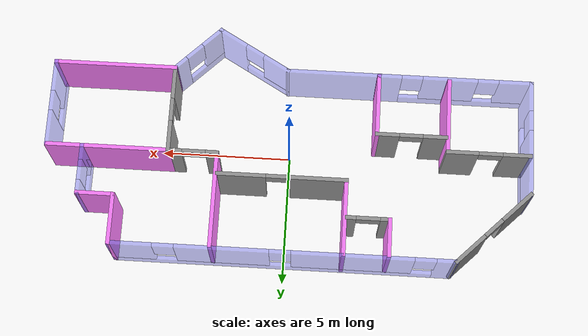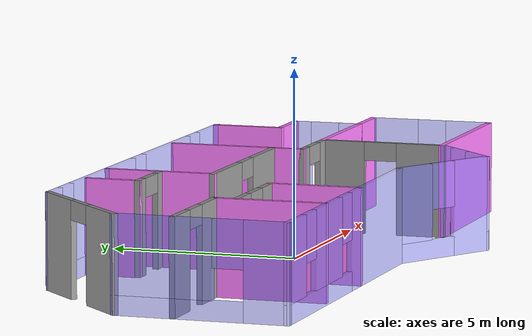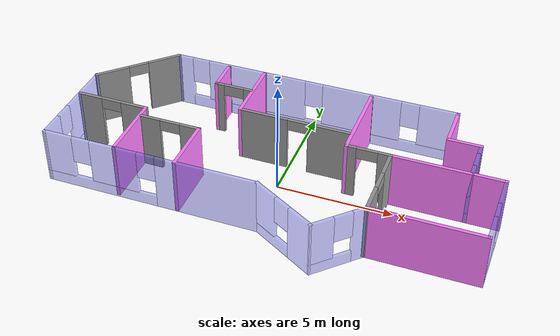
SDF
<?xml version='1.0'?>
<sdf version='1.6'>
  <model name='house'>
    <link name='Wall_10'>
      <pose frame=''>3.72086 -3.525 0 0 0 -2.35619</pose>
      <self_collide>0</self_collide>
      <kinematic>0</kinematic>
      <gravity>1</gravity>
      <inertial>
        <mass>1</mass>
        <pose frame=''>0 0 0 0 -0 0</pose>
        <inertia>
          <ixx>1</ixx>
          <ixy>0</ixy>
          <ixz>0</ixz>
          <iyy>1</iyy>
          <iyz>0</iyz>
          <izz>1</izz>
        </inertia>
      </inertial>
      <visual name='Wall_10_Visual_0'>
        <pose frame=''>-0.917996 0 1.25 0 -0 0</pose>
        <geometry>
          <box>
            <size>0.664008 0.15 2.5</size>
          </box>
        </geometry>
        <material>
          <script>
            <uri>file://media/materials/scripts/gazebo.material</uri>
            <name>Gazebo/Grey</name>
          </script>
          <ambient>0.5 0.5 1 0.5</ambient>
          <shader type='pixel'>
            <normal_map>__default__</normal_map>
          </shader>
          <diffuse>0.7 0.7 0.7 1</diffuse>
          <specular>0.01 0.01 0.01 1</specular>
          <emissive>0 0 0 1</emissive>
        </material>
        <meta>
          <layer>0</layer>
        </meta>
        <transparency>0</transparency>
        <cast_shadows>1</cast_shadows>
      </visual>
      <visual name='Wall_10_Visual_1'>
        <pose frame=''>0.332004 0 0.25 0 -0 0</pose>
        <geometry>
          <box>
            <size>1.83599 0.15 0.5</size>
          </box>
        </geometry>
        <material>
          <script>
            <uri>file://media/materials/scripts/gazebo.material</uri>
            <name>Gazebo/Grey</name>
          </script>
          <ambient>0.5 0.5 1 0.5</ambient>
          <shader type='pixel'>
            <normal_map>__default__</normal_map>
          </shader>
          <diffuse>0.7 0.7 0.7 1</diffuse>
          <specular>0.01 0.01 0.01 1</specular>
          <emissive>0 0 0 1</emissive>
        </material>
        <meta>
          <layer>0</layer>
        </meta>
        <transparency>0</transparency>
        <cast_shadows>1</cast_shadows>
      </visual>
      <visual name='Wall_10_Visual_2'>
        <pose frame=''>0.732004 0 1.5 0 -0 0</pose>
        <geometry>
          <box>
            <size>1.03599 0.15 2</size>
          </box>
        </geometry>
        <material>
          <script>
            <uri>file://media/materials/scripts/gazebo.material</uri>
            <name>Gazebo/Grey</name>
          </script>
          <ambient>0.5 0.5 1 0.5</ambient>
          <shader type='pixel'>
            <normal_map>__default__</normal_map>
          </shader>
          <diffuse>0.7 0.7 0.7 1</diffuse>
          <specular>0.01 0.01 0.01 1</specular>
          <emissive>0 0 0 1</emissive>
        </material>
        <meta>
          <layer>0</layer>
        </meta>
        <transparency>0</transparency>
        <cast_shadows>1</cast_shadows>
      </visual>
      <visual name='Wall_10_Visual_3'>
        <pose frame=''>-0.185992 0 1.9 0 -0 0</pose>
        <geometry>
          <box>
            <size>0.8 0.15 1.2</size>
          </box>
        </geometry>
        <material>
          <script>
            <uri>file://media/materials/scripts/gazebo.material</uri>
            <name>Gazebo/Grey</name>
          </script>
          <ambient>0.5 0.5 1 0.5</ambient>
          <shader type='pixel'>
            <normal_map>__default__</normal_map>
          </shader>
          <diffuse>0.7 0.7 0.7 1</diffuse>
          <specular>0.01 0.01 0.01 1</specular>
          <emissive>0 0 0 1</emissive>
        </material>
        <meta>
          <layer>0</layer>
        </meta>
        <transparency>0</transparency>
        <cast_shadows>1</cast_shadows>
      </visual>
      <collision name='Wall_10_Collision_0'>
        <laser_retro>0</laser_retro>
        <max_contacts>10</max_contacts>
        <pose frame=''>-0.917996 0 1.25 0 -0 0</pose>
        <geometry>
          <box>
            <size>0.664008 0.15 2.5</size>
          </box>
        </geometry>
        <surface>
          <friction>
            <ode>
              <mu>1</mu>
              <mu2>1</mu2>
              <fdir1>0 0 0</fdir1>
              <slip1>0</slip1>
              <slip2>0</slip2>
            </ode>
            <torsional>
              <coefficient>1</coefficient>
              <patch_radius>0</patch_radius>
              <surface_radius>0</surface_radius>
              <use_patch_radius>1</use_patch_radius>
              <ode>
                <slip>0</slip>
              </ode>
            </torsional>
          </friction>
          <bounce>
            <restitution_coefficient>0</restitution_coefficient>
            <threshold>1e+06</threshold>
          </bounce>
          <contact>
            <collide_without_contact>0</collide_without_contact>
            <collide_without_contact_bitmask>1</collide_without_contact_bitmask>
            <collide_bitmask>1</collide_bitmask>
            <ode>
              <soft_cfm>0</soft_cfm>
              <soft_erp>0.2</soft_erp>
              <kp>1e+13</kp>
              <kd>1</kd>
              <max_vel>0.01</max_vel>
              <min_depth>0</min_depth>
            </ode>
            <bullet>
              <split_impulse>1</split_impulse>
              <split_impulse_penetration_threshold>-0.01</split_impulse_penetration_threshold>
              <soft_cfm>0</soft_cfm>
              <soft_erp>0.2</soft_erp>
              <kp>1e+13</kp>
              <kd>1</kd>
            </bullet>
          </contact>
        </surface>
      </collision>
      <collision name='Wall_10_Collision_1'>
        <laser_retro>0</laser_retro>
        <max_contacts>10</max_contacts>
        <pose frame=''>0.332004 0 0.25 0 -0 0</pose>
        <geometry>
          <box>
            <size>1.83599 0.15 0.5</size>
          </box>
        </geometry>
        <surface>
          <friction>
            <ode>
              <mu>1</mu>
              <mu2>1</mu2>
              <fdir1>0 0 0</fdir1>
              <slip1>0</slip1>
              <slip2>0</slip2>
            </ode>
            <torsional>
              <coefficient>1</coefficient>
              <patch_radius>0</patch_radius>
              <surface_radius>0</surface_radius>
              <use_patch_radius>1</use_patch_radius>
              <ode>
                <slip>0</slip>
              </ode>
            </torsional>
          </friction>
          <bounce>
            <restitution_coefficient>0</restitution_coefficient>
            <threshold>1e+06</threshold>
          </bounce>
          <contact>
            <collide_without_contact>0</collide_without_contact>
            <collide_without_contact_bitmask>1</collide_without_contact_bitmask>
            <collide_bitmask>1</collide_bitmask>
            <ode>
              <soft_cfm>0</soft_cfm>
              <soft_erp>0.2</soft_erp>
              <kp>1e+13</kp>
              <kd>1</kd>
              <max_vel>0.01</max_vel>
              <min_depth>0</min_depth>
            </ode>
            <bullet>
              <split_impulse>1</split_impulse>
              <split_impulse_penetration_threshold>-0.01</split_impulse_penetration_threshold>
              <soft_cfm>0</soft_cfm>
              <soft_erp>0.2</soft_erp>
              <kp>1e+13</kp>
              <kd>1</kd>
            </bullet>
          </contact>
        </surface>
      </collision>
      <collision name='Wall_10_Collision_2'>
        <laser_retro>0</laser_retro>
        <max_contacts>10</max_contacts>
        <pose frame=''>0.732004 0 1.5 0 -0 0</pose>
        <geometry>
          <box>
            <size>1.03599 0.15 2</size>
          </box>
        </geometry>
        <surface>
          <friction>
            <ode>
              <mu>1</mu>
              <mu2>1</mu2>
              <fdir1>0 0 0</fdir1>
              <slip1>0</slip1>
              <slip2>0</slip2>
            </ode>
            <torsional>
              <coefficient>1</coefficient>
              <patch_radius>0</patch_radius>
              <surface_radius>0</surface_radius>
              <use_patch_radius>1</use_patch_radius>
              <ode>
                <slip>0</slip>
              </ode>
            </torsional>
          </friction>
          <bounce>
            <restitution_coefficient>0</restitution_coefficient>
            <threshold>1e+06</threshold>
          </bounce>
          <contact>
            <collide_without_contact>0</collide_without_contact>
            <collide_without_contact_bitmask>1</collide_without_contact_bitmask>
            <collide_bitmask>1</collide_bitmask>
            <ode>
              <soft_cfm>0</soft_cfm>
              <soft_erp>0.2</soft_erp>
              <kp>1e+13</kp>
              <kd>1</kd>
              <max_vel>0.01</max_vel>
              <min_depth>0</min_depth>
            </ode>
            <bullet>
              <split_impulse>1</split_impulse>
              <split_impulse_penetration_threshold>-0.01</split_impulse_penetration_threshold>
              <soft_cfm>0</soft_cfm>
              <soft_erp>0.2</soft_erp>
              <kp>1e+13</kp>
              <kd>1</kd>
            </bullet>
          </contact>
        </surface>
      </collision>
      <collision name='Wall_10_Collision_3'>
        <laser_retro>0</laser_retro>
        <max_contacts>10</max_contacts>
        <pose frame=''>-0.185992 0 1.9 0 -0 0</pose>
        <geometry>
          <box>
            <size>0.8 0.15 1.2</size>
          </box>
        </geometry>
        <surface>
          <friction>
            <ode>
              <mu>1</mu>
              <mu2>1</mu2>
              <fdir1>0 0 0</fdir1>
              <slip1>0</slip1>
              <slip2>0</slip2>
            </ode>
            <torsional>
              <coefficient>1</coefficient>
              <patch_radius>0</patch_radius>
              <surface_radius>0</surface_radius>
              <use_patch_radius>1</use_patch_radius>
              <ode>
                <slip>0</slip>
              </ode>
            </torsional>
          </friction>
          <bounce>
            <restitution_coefficient>0</restitution_coefficient>
            <threshold>1e+06</threshold>
          </bounce>
          <contact>
            <collide_without_contact>0</collide_without_contact>
            <collide_without_contact_bitmask>1</collide_without_contact_bitmask>
            <collide_bitmask>1</collide_bitmask>
            <ode>
              <soft_cfm>0</soft_cfm>
              <soft_erp>0.2</soft_erp>
              <kp>1e+13</kp>
              <kd>1</kd>
              <max_vel>0.01</max_vel>
              <min_depth>0</min_depth>
            </ode>
            <bullet>
              <split_impulse>1</split_impulse>
              <split_impulse_penetration_threshold>-0.01</split_impulse_penetration_threshold>
              <soft_cfm>0</soft_cfm>
              <soft_erp>0.2</soft_erp>
              <kp>1e+13</kp>
              <kd>1</kd>
            </bullet>
          </contact>
        </surface>
      </collision>
    </link>
    <link name='Wall_11'>
      <pose frame=''>1.54767 -3.58085 0 0 -0 2.61799</pose>
      <self_collide>0</self_collide>
      <kinematic>0</kinematic>
      <gravity>1</gravity>
      <inertial>
        <mass>1</mass>
        <pose frame=''>0 0 0 0 -0 0</pose>
        <inertia>
          <ixx>1</ixx>
          <ixy>0</ixy>
          <ixz>0</ixz>
          <iyy>1</iyy>
          <iyz>0</iyz>
          <izz>1</izz>
        </inertia>
      </inertial>
      <visual name='Wall_11_Visual_0'>
        <pose frame=''>-0.990098 0 1.25 0 -0 0</pose>
        <geometry>
          <box>
            <size>1.2698 0.15 2.5</size>
          </box>
        </geometry>
        <material>
          <script>
            <uri>file://media/materials/scripts/gazebo.material</uri>
            <name>Gazebo/Grey</name>
          </script>
          <ambient>0.5 0.5 1 0.5</ambient>
          <shader type='pixel'>
            <normal_map>__default__</normal_map>
          </shader>
          <diffuse>0.7 0.7 0.7 1</diffuse>
          <specular>0.01 0.01 0.01 1</specular>
          <emissive>0 0 0 1</emissive>
        </material>
        <meta>
          <layer>0</layer>
        </meta>
        <transparency>0</transparency>
        <cast_shadows>1</cast_shadows>
      </visual>
      <visual name='Wall_11_Visual_1'>
        <pose frame=''>0.634902 0 0.25 0 -0 0</pose>
        <geometry>
          <box>
            <size>1.9802 0.15 0.5</size>
          </box>
        </geometry>
        <material>
          <script>
            <uri>file://media/materials/scripts/gazebo.material</uri>
            <name>Gazebo/Grey</name>
          </script>
          <ambient>0.5 0.5 1 0.5</ambient>
          <shader type='pixel'>
            <normal_map>__default__</normal_map>
          </shader>
          <diffuse>0.7 0.7 0.7 1</diffuse>
          <specular>0.01 0.01 0.01 1</specular>
          <emissive>0 0 0 1</emissive>
        </material>
        <meta>
          <layer>0</layer>
        </meta>
        <transparency>0</transparency>
        <cast_shadows>1</cast_shadows>
      </visual>
      <visual name='Wall_11_Visual_2'>
        <pose frame=''>1.0349 0 1.5 0 -0 0</pose>
        <geometry>
          <box>
            <size>1.1802 0.15 2</size>
          </box>
        </geometry>
        <material>
          <script>
            <uri>file://media/materials/scripts/gazebo.material</uri>
            <name>Gazebo/Grey</name>
          </script>
          <ambient>0.5 0.5 1 0.5</ambient>
          <shader type='pixel'>
            <normal_map>__default__</normal_map>
          </shader>
          <diffuse>0.7 0.7 0.7 1</diffuse>
          <specular>0.01 0.01 0.01 1</specular>
          <emissive>0 0 0 1</emissive>
        </material>
        <meta>
          <layer>0</layer>
        </meta>
        <transparency>0</transparency>
        <cast_shadows>1</cast_shadows>
      </visual>
      <visual name='Wall_11_Visual_3'>
        <pose frame=''>0.044803 0 1.9 0 -0 0</pose>
        <geometry>
          <box>
            <size>0.8 0.15 1.2</size>
          </box>
        </geometry>
        <material>
          <script>
            <uri>file://media/materials/scripts/gazebo.material</uri>
            <name>Gazebo/Grey</name>
          </script>
          <ambient>0.5 0.5 1 0.5</ambient>
          <shader type='pixel'>
            <normal_map>__default__</normal_map>
          </shader>
          <diffuse>0.7 0.7 0.7 1</diffuse>
          <specular>0.01 0.01 0.01 1</specular>
          <emissive>0 0 0 1</emissive>
        </material>
        <meta>
          <layer>0</layer>
        </meta>
        <transparency>0</transparency>
        <cast_shadows>1</cast_shadows>
      </visual>
      <collision name='Wall_11_Collision_0'>
        <laser_retro>0</laser_retro>
        <max_contacts>10</max_contacts>
        <pose frame=''>-0.990098 0 1.25 0 -0 0</pose>
        <geometry>
          <box>
            <size>1.2698 0.15 2.5</size>
          </box>
        </geometry>
        <surface>
          <friction>
            <ode>
              <mu>1</mu>
              <mu2>1</mu2>
              <fdir1>0 0 0</fdir1>
              <slip1>0</slip1>
              <slip2>0</slip2>
            </ode>
            <torsional>
              <coefficient>1</coefficient>
              <patch_radius>0</patch_radius>
              <surface_radius>0</surface_radius>
              <use_patch_radius>1</use_patch_radius>
              <ode>
                <slip>0</slip>
              </ode>
            </torsional>
          </friction>
          <bounce>
            <restitution_coefficient>0</restitution_coefficient>
            <threshold>1e+06</threshold>
          </bounce>
          <contact>
            <collide_without_contact>0</collide_without_contact>
            <collide_without_contact_bitmask>1</collide_without_contact_bitmask>
            <collide_bitmask>1</collide_bitmask>
            <ode>
              <soft_cfm>0</soft_cfm>
              <soft_erp>0.2</soft_erp>
              <kp>1e+13</kp>
              <kd>1</kd>
              <max_vel>0.01</max_vel>
              <min_depth>0</min_depth>
            </ode>
            <bullet>
              <split_impulse>1</split_impulse>
              <split_impulse_penetration_threshold>-0.01</split_impulse_penetration_threshold>
              <soft_cfm>0</soft_cfm>
              <soft_erp>0.2</soft_erp>
              <kp>1e+13</kp>
              <kd>1</kd>
            </bullet>
          </contact>
        </surface>
      </collision>
      <collision name='Wall_11_Collision_1'>
        <laser_retro>0</laser_retro>
        <max_contacts>10</max_contacts>
        <pose frame=''>0.634902 0 0.25 0 -0 0</pose>
        <geometry>
          <box>
            <size>1.9802 0.15 0.5</size>
          </box>
        </geometry>
        <surface>
          <friction>
            <ode>
              <mu>1</mu>
              <mu2>1</mu2>
              <fdir1>0 0 0</fdir1>
              <slip1>0</slip1>
              <slip2>0</slip2>
            </ode>
            <torsional>
              <coefficient>1</coefficient>
              <patch_radius>0</patch_radius>
              <surface_radius>0</surface_radius>
              <use_patch_radius>1</use_patch_radius>
              <ode>
                <slip>0</slip>
              </ode>
            </torsional>
          </friction>
          <bounce>
            <restitution_coefficient>0</restitution_coefficient>
            <threshold>1e+06</threshold>
          </bounce>
          <contact>
            <collide_without_contact>0</collide_without_contact>
            <collide_without_contact_bitmask>1</collide_without_contact_bitmask>
            <collide_bitmask>1</collide_bitmask>
            <ode>
              <soft_cfm>0</soft_cfm>
              <soft_erp>0.2</soft_erp>
              <kp>1e+13</kp>
              <kd>1</kd>
              <max_vel>0.01</max_vel>
              <min_depth>0</min_depth>
            </ode>
            <bullet>
              <split_impulse>1</split_impulse>
              <split_impulse_penetration_threshold>-0.01</split_impulse_penetration_threshold>
              <soft_cfm>0</soft_cfm>
              <soft_erp>0.2</soft_erp>
              <kp>1e+13</kp>
              <kd>1</kd>
            </bullet>
          </contact>
        </surface>
      </collision>
      <collision name='Wall_11_Collision_2'>
        <laser_retro>0</laser_retro>
        <max_contacts>10</max_contacts>
        <pose frame=''>1.0349 0 1.5 0 -0 0</pose>
        <geometry>
          <box>
            <size>1.1802 0.15 2</size>
          </box>
        </geometry>
        <surface>
          <friction>
            <ode>
              <mu>1</mu>
              <mu2>1</mu2>
              <fdir1>0 0 0</fdir1>
              <slip1>0</slip1>
              <slip2>0</slip2>
            </ode>
            <torsional>
              <coefficient>1</coefficient>
              <patch_radius>0</patch_radius>
              <surface_radius>0</surface_radius>
              <use_patch_radius>1</use_patch_radius>
              <ode>
                <slip>0</slip>
              </ode>
            </torsional>
          </friction>
          <bounce>
            <restitution_coefficient>0</restitution_coefficient>
            <threshold>1e+06</threshold>
          </bounce>
          <contact>
            <collide_without_contact>0</collide_without_contact>
            <collide_without_contact_bitmask>1</collide_without_contact_bitmask>
            <collide_bitmask>1</collide_bitmask>
            <ode>
              <soft_cfm>0</soft_cfm>
              <soft_erp>0.2</soft_erp>
              <kp>1e+13</kp>
              <kd>1</kd>
              <max_vel>0.01</max_vel>
              <min_depth>0</min_depth>
            </ode>
            <bullet>
              <split_impulse>1</split_impulse>
              <split_impulse_penetration_threshold>-0.01</split_impulse_penetration_threshold>
              <soft_cfm>0</soft_cfm>
              <soft_erp>0.2</soft_erp>
              <kp>1e+13</kp>
              <kd>1</kd>
            </bullet>
          </contact>
        </surface>
      </collision>
      <collision name='Wall_11_Collision_3'>
        <laser_retro>0</laser_retro>
        <max_contacts>10</max_contacts>
        <pose frame=''>0.044803 0 1.9 0 -0 0</pose>
        <geometry>
          <box>
            <size>0.8 0.15 1.2</size>
          </box>
        </geometry>
        <surface>
          <friction>
            <ode>
              <mu>1</mu>
              <mu2>1</mu2>
              <fdir1>0 0 0</fdir1>
              <slip1>0</slip1>
              <slip2>0</slip2>
            </ode>
            <torsional>
              <coefficient>1</coefficient>
              <patch_radius>0</patch_radius>
              <surface_radius>0</surface_radius>
              <use_patch_radius>1</use_patch_radius>
              <ode>
                <slip>0</slip>
              </ode>
            </torsional>
          </friction>
          <bounce>
            <restitution_coefficient>0</restitution_coefficient>
            <threshold>1e+06</threshold>
          </bounce>
          <contact>
            <collide_without_contact>0</collide_without_contact>
            <collide_without_contact_bitmask>1</collide_without_contact_bitmask>
            <collide_bitmask>1</collide_bitmask>
            <ode>
              <soft_cfm>0</soft_cfm>
              <soft_erp>0.2</soft_erp>
              <kp>1e+13</kp>
              <kd>1</kd>
              <max_vel>0.01</max_vel>
              <min_depth>0</min_depth>
            </ode>
            <bullet>
              <split_impulse>1</split_impulse>
              <split_impulse_penetration_threshold>-0.01</split_impulse_penetration_threshold>
              <soft_cfm>0</soft_cfm>
              <soft_erp>0.2</soft_erp>
              <kp>1e+13</kp>
              <kd>1</kd>
            </bullet>
          </contact>
        </surface>
      </collision>
    </link>
    <link name='Wall_12'>
      <pose frame=''>-4.46967 -2.80585 0 0 -0 3.14159</pose>
      <self_collide>0</self_collide>
      <kinematic>0</kinematic>
      <gravity>1</gravity>
      <inertial>
        <mass>1</mass>
        <pose frame=''>0 0 0 0 -0 0</pose>
        <inertia>
          <ixx>1</ixx>
          <ixy>0</ixy>
          <ixz>0</ixz>
          <iyy>1</iyy>
          <iyz>0</iyz>
          <izz>1</izz>
        </inertia>
      </inertial>
      <visual name='Wall_12_Visual_0'>
        <pose frame=''>-2.52226 0 1.25 0 -0 0</pose>
        <geometry>
          <box>
            <size>4.45547 0.15 2.5</size>
          </box>
        </geometry>
        <material>
          <script>
            <uri>file://media/materials/scripts/gazebo.material</uri>
            <name>Gazebo/Grey</name>
          </script>
          <ambient>0.5 0.5 1 0.5</ambient>
          <shader type='pixel'>
            <normal_map>__default__</normal_map>
          </shader>
          <diffuse>0.7 0.7 0.7 1</diffuse>
          <specular>0.01 0.01 0.01 1</specular>
          <emissive>0 0 0 1</emissive>
        </material>
        <meta>
          <layer>0</layer>
        </meta>
        <transparency>0</transparency>
        <cast_shadows>1</cast_shadows>
      </visual>
      <visual name='Wall_12_Visual_1'>
        <pose frame=''>2.22774 0 0.25 0 -0 0</pose>
        <geometry>
          <box>
            <size>5.04453 0.15 0.5</size>
          </box>
        </geometry>
        <material>
          <script>
            <uri>file://media/materials/scripts/gazebo.material</uri>
            <name>Gazebo/Grey</name>
          </script>
          <ambient>0.5 0.5 1 0.5</ambient>
          <shader type='pixel'>
            <normal_map>__default__</normal_map>
          </shader>
          <diffuse>0.7 0.7 0.7 1</diffuse>
          <specular>0.01 0.01 0.01 1</specular>
          <emissive>0 0 0 1</emissive>
        </material>
        <meta>
          <layer>0</layer>
        </meta>
        <transparency>0</transparency>
        <cast_shadows>1</cast_shadows>
      </visual>
      <visual name='Wall_12_Visual_5'>
        <pose frame=''>3.01993 0 1.9 0 -0 0</pose>
        <geometry>
          <box>
            <size>0.8 0.15 1.2</size>
          </box>
        </geometry>
        <material>
          <script>
            <uri>file://media/materials/scripts/gazebo.material</uri>
            <name>Gazebo/Grey</name>
          </script>
          <ambient>0.5 0.5 1 0.5</ambient>
          <shader type='pixel'>
            <normal_map>__default__</normal_map>
          </shader>
          <diffuse>0.7 0.7 0.7 1</diffuse>
          <specular>0.01 0.01 0.01 1</specular>
          <emissive>0 0 0 1</emissive>
        </material>
        <meta>
          <layer>0</layer>
        </meta>
        <transparency>0</transparency>
        <cast_shadows>1</cast_shadows>
      </visual>
      <visual name='Wall_12_Visual_2'>
        <pose frame=''>1.5627 0 1.5 0 -0 0</pose>
        <geometry>
          <box>
            <size>2.11446 0.15 2</size>
          </box>
        </geometry>
        <material>
          <script>
            <uri>file://media/materials/scripts/gazebo.material</uri>
            <name>Gazebo/Grey</name>
          </script>
          <ambient>0.5 0.5 1 0.5</ambient>
          <shader type='pixel'>
            <normal_map>__default__</normal_map>
          </shader>
          <diffuse>0.7 0.7 0.7 1</diffuse>
          <specular>0.01 0.01 0.01 1</specular>
          <emissive>0 0 0 1</emissive>
        </material>
        <meta>
          <layer>0</layer>
        </meta>
        <transparency>0</transparency>
        <cast_shadows>1</cast_shadows>
      </visual>
      <visual name='Wall_12_Visual_3'>
        <pose frame=''>4.08496 0 1.5 0 -0 0</pose>
        <geometry>
          <box>
            <size>1.33007 0.15 2</size>
          </box>
        </geometry>
        <material>
          <script>
            <uri>file://media/materials/scripts/gazebo.material</uri>
            <name>Gazebo/Grey</name>
          </script>
          <ambient>0.5 0.5 1 0.5</ambient>
          <shader type='pixel'>
            <normal_map>__default__</normal_map>
          </shader>
          <diffuse>0.7 0.7 0.7 1</diffuse>
          <specular>0.01 0.01 0.01 1</specular>
          <emissive>0 0 0 1</emissive>
        </material>
        <meta>
          <layer>0</layer>
        </meta>
        <transparency>0</transparency>
        <cast_shadows>1</cast_shadows>
      </visual>
      <visual name='Wall_12_Visual_4'>
        <pose frame=''>0.10547 0 1.9 0 -0 0</pose>
        <geometry>
          <box>
            <size>0.8 0.15 1.2</size>
          </box>
        </geometry>
        <material>
          <script>
            <uri>file://media/materials/scripts/gazebo.material</uri>
            <name>Gazebo/Grey</name>
          </script>
          <ambient>0.5 0.5 1 0.5</ambient>
          <shader type='pixel'>
            <normal_map>__default__</normal_map>
          </shader>
          <diffuse>0.7 0.7 0.7 1</diffuse>
          <specular>0.01 0.01 0.01 1</specular>
          <emissive>0 0 0 1</emissive>
        </material>
        <meta>
          <layer>0</layer>
        </meta>
        <transparency>0</transparency>
        <cast_shadows>1</cast_shadows>
      </visual>
      <collision name='Wall_12_Collision_0'>
        <laser_retro>0</laser_retro>
        <max_contacts>10</max_contacts>
        <pose frame=''>-2.52226 0 1.25 0 -0 0</pose>
        <geometry>
          <box>
            <size>4.45547 0.15 2.5</size>
          </box>
        </geometry>
        <surface>
          <friction>
            <ode>
              <mu>1</mu>
              <mu2>1</mu2>
              <fdir1>0 0 0</fdir1>
              <slip1>0</slip1>
              <slip2>0</slip2>
            </ode>
            <torsional>
              <coefficient>1</coefficient>
              <patch_radius>0</patch_radius>
              <surface_radius>0</surface_radius>
              <use_patch_radius>1</use_patch_radius>
              <ode>
                <slip>0</slip>
              </ode>
            </torsional>
          </friction>
          <bounce>
            <restitution_coefficient>0</restitution_coefficient>
            <threshold>1e+06</threshold>
          </bounce>
          <contact>
            <collide_without_contact>0</collide_without_contact>
            <collide_without_contact_bitmask>1</collide_without_contact_bitmask>
            <collide_bitmask>1</collide_bitmask>
            <ode>
              <soft_cfm>0</soft_cfm>
              <soft_erp>0.2</soft_erp>
              <kp>1e+13</kp>
              <kd>1</kd>
              <max_vel>0.01</max_vel>
              <min_depth>0</min_depth>
            </ode>
            <bullet>
              <split_impulse>1</split_impulse>
              <split_impulse_penetration_threshold>-0.01</split_impulse_penetration_threshold>
              <soft_cfm>0</soft_cfm>
              <soft_erp>0.2</soft_erp>
              <kp>1e+13</kp>
              <kd>1</kd>
            </bullet>
          </contact>
        </surface>
      </collision>
      <collision name='Wall_12_Collision_1'>
        <laser_retro>0</laser_retro>
        <max_contacts>10</max_contacts>
        <pose frame=''>2.22774 0 0.25 0 -0 0</pose>
        <geometry>
          <box>
            <size>5.04453 0.15 0.5</size>
          </box>
        </geometry>
        <surface>
          <friction>
            <ode>
              <mu>1</mu>
              <mu2>1</mu2>
              <fdir1>0 0 0</fdir1>
              <slip1>0</slip1>
              <slip2>0</slip2>
            </ode>
            <torsional>
              <coefficient>1</coefficient>
              <patch_radius>0</patch_radius>
              <surface_radius>0</surface_radius>
              <use_patch_radius>1</use_patch_radius>
              <ode>
                <slip>0</slip>
              </ode>
            </torsional>
          </friction>
          <bounce>
            <restitution_coefficient>0</restitution_coefficient>
            <threshold>1e+06</threshold>
          </bounce>
          <contact>
            <collide_without_contact>0</collide_without_contact>
            <collide_without_contact_bitmask>1</collide_without_contact_bitmask>
            <collide_bitmask>1</collide_bitmask>
            <ode>
              <soft_cfm>0</soft_cfm>
              <soft_erp>0.2</soft_erp>
              <kp>1e+13</kp>
              <kd>1</kd>
              <max_vel>0.01</max_vel>
              <min_depth>0</min_depth>
            </ode>
            <bullet>
              <split_impulse>1</split_impulse>
              <split_impulse_penetration_threshold>-0.01</split_impulse_penetration_threshold>
              <soft_cfm>0</soft_cfm>
              <soft_erp>0.2</soft_erp>
              <kp>1e+13</kp>
              <kd>1</kd>
            </bullet>
          </contact>
        </surface>
      </collision>
      <collision name='Wall_12_Collision_5'>
        <laser_retro>0</laser_retro>
        <max_contacts>10</max_contacts>
        <pose frame=''>3.01993 0 1.9 0 -0 0</pose>
        <geometry>
          <box>
            <size>0.8 0.15 1.2</size>
          </box>
        </geometry>
        <surface>
          <friction>
            <ode>
              <mu>1</mu>
              <mu2>1</mu2>
              <fdir1>0 0 0</fdir1>
              <slip1>0</slip1>
              <slip2>0</slip2>
            </ode>
            <torsional>
              <coefficient>1</coefficient>
              <patch_radius>0</patch_radius>
              <surface_radius>0</surface_radius>
              <use_patch_radius>1</use_patch_radius>
              <ode>
                <slip>0</slip>
              </ode>
            </torsional>
          </friction>
          <bounce>
            <restitution_coefficient>0</restitution_coefficient>
            <threshold>1e+06</threshold>
          </bounce>
          <contact>
            <collide_without_contact>0</collide_without_contact>
            <collide_without_contact_bitmask>1</collide_without_contact_bitmask>
            <collide_bitmask>1</collide_bitmask>
            <ode>
              <soft_cfm>0</soft_cfm>
              <soft_erp>0.2</soft_erp>
              <kp>1e+13</kp>
              <kd>1</kd>
              <max_vel>0.01</max_vel>
              <min_depth>0</min_depth>
            </ode>
            <bullet>
              <split_impulse>1</split_impulse>
              <split_impulse_penetration_threshold>-0.01</split_impulse_penetration_threshold>
              <soft_cfm>0</soft_cfm>
              <soft_erp>0.2</soft_erp>
              <kp>1e+13</kp>
              <kd>1</kd>
            </bullet>
          </contact>
        </surface>
      </collision>
      <collision name='Wall_12_Collision_2'>
        <laser_retro>0</laser_retro>
        <max_contacts>10</max_contacts>
        <pose frame=''>1.5627 0 1.5 0 -0 0</pose>
        <geometry>
          <box>
            <size>2.11446 0.15 2</size>
          </box>
        </geometry>
        <surface>
          <friction>
            <ode>
              <mu>1</mu>
              <mu2>1</mu2>
              <fdir1>0 0 0</fdir1>
              <slip1>0</slip1>
              <slip2>0</slip2>
            </ode>
            <torsional>
              <coefficient>1</coefficient>
              <patch_radius>0</patch_radius>
              <surface_radius>0</surface_radius>
              <use_patch_radius>1</use_patch_radius>
              <ode>
                <slip>0</slip>
              </ode>
            </torsional>
          </friction>
          <bounce>
            <restitution_coefficient>0</restitution_coefficient>
            <threshold>1e+06</threshold>
          </bounce>
          <contact>
            <collide_without_contact>0</collide_without_contact>
            <collide_without_contact_bitmask>1</collide_without_contact_bitmask>
            <collide_bitmask>1</collide_bitmask>
            <ode>
              <soft_cfm>0</soft_cfm>
              <soft_erp>0.2</soft_erp>
              <kp>1e+13</kp>
              <kd>1</kd>
              <max_vel>0.01</max_vel>
              <min_depth>0</min_depth>
            </ode>
            <bullet>
              <split_impulse>1</split_impulse>
              <split_impulse_penetration_threshold>-0.01</split_impulse_penetration_threshold>
              <soft_cfm>0</soft_cfm>
              <soft_erp>0.2</soft_erp>
              <kp>1e+13</kp>
              <kd>1</kd>
            </bullet>
          </contact>
        </surface>
      </collision>
      <collision name='Wall_12_Collision_3'>
        <laser_retro>0</laser_retro>
        <max_contacts>10</max_contacts>
        <pose frame=''>4.08496 0 1.5 0 -0 0</pose>
        <geometry>
          <box>
            <size>1.33007 0.15 2</size>
          </box>
        </geometry>
        <surface>
          <friction>
            <ode>
              <mu>1</mu>
              <mu2>1</mu2>
              <fdir1>0 0 0</fdir1>
              <slip1>0</slip1>
              <slip2>0</slip2>
            </ode>
            <torsional>
              <coefficient>1</coefficient>
              <patch_radius>0</patch_radius>
              <surface_radius>0</surface_radius>
              <use_patch_radius>1</use_patch_radius>
              <ode>
                <slip>0</slip>
              </ode>
            </torsional>
          </friction>
          <bounce>
            <restitution_coefficient>0</restitution_coefficient>
            <threshold>1e+06</threshold>
          </bounce>
          <contact>
            <collide_without_contact>0</collide_without_contact>
            <collide_without_contact_bitmask>1</collide_without_contact_bitmask>
            <collide_bitmask>1</collide_bitmask>
            <ode>
              <soft_cfm>0</soft_cfm>
              <soft_erp>0.2</soft_erp>
              <kp>1e+13</kp>
              <kd>1</kd>
              <max_vel>0.01</max_vel>
              <min_depth>0</min_depth>
            </ode>
            <bullet>
              <split_impulse>1</split_impulse>
              <split_impulse_penetration_threshold>-0.01</split_impulse_penetration_threshold>
              <soft_cfm>0</soft_cfm>
              <soft_erp>0.2</soft_erp>
              <kp>1e+13</kp>
              <kd>1</kd>
            </bullet>
          </contact>
        </surface>
      </collision>
      <collision name='Wall_12_Collision_4'>
        <laser_retro>0</laser_retro>
        <max_contacts>10</max_contacts>
        <pose frame=''>0.10547 0 1.9 0 -0 0</pose>
        <geometry>
          <box>
            <size>0.8 0.15 1.2</size>
          </box>
        </geometry>
        <surface>
          <friction>
            <ode>
              <mu>1</mu>
              <mu2>1</mu2>
              <fdir1>0 0 0</fdir1>
              <slip1>0</slip1>
              <slip2>0</slip2>
            </ode>
            <torsional>
              <coefficient>1</coefficient>
              <patch_radius>0</patch_radius>
              <surface_radius>0</surface_radius>
              <use_patch_radius>1</use_patch_radius>
              <ode>
                <slip>0</slip>
              </ode>
            </torsional>
          </friction>
          <bounce>
            <restitution_coefficient>0</restitution_coefficient>
            <threshold>1e+06</threshold>
          </bounce>
          <contact>
            <collide_without_contact>0</collide_without_contact>
            <collide_without_contact_bitmask>1</collide_without_contact_bitmask>
            <collide_bitmask>1</collide_bitmask>
            <ode>
              <soft_cfm>0</soft_cfm>
              <soft_erp>0.2</soft_erp>
              <kp>1e+13</kp>
              <kd>1</kd>
              <max_vel>0.01</max_vel>
              <min_depth>0</min_depth>
            </ode>
            <bullet>
              <split_impulse>1</split_impulse>
              <split_impulse_penetration_threshold>-0.01</split_impulse_penetration_threshold>
              <soft_cfm>0</soft_cfm>
              <soft_erp>0.2</soft_erp>
              <kp>1e+13</kp>
              <kd>1</kd>
            </bullet>
          </contact>
        </surface>
      </collision>
    </link>
    <link name='Wall_13'>
      <pose frame=''>-9.13266 -0.586181 0 0 -0 1.56539</pose>
      <self_collide>0</self_collide>
      <kinematic>0</kinematic>
      <gravity>1</gravity>
      <inertial>
        <mass>1</mass>
        <pose frame=''>0 0 0 0 -0 0</pose>
        <inertia>
          <ixx>1</ixx>
          <ixy>0</ixy>
          <ixz>0</ixz>
          <iyy>1</iyy>
          <iyz>0</iyz>
          <izz>1</izz>
        </inertia>
      </inertial>
      <visual name='Wall_13_Visual_0'>
        <pose frame=''>-1.70872 0 1.25 0 -0 0</pose>
        <geometry>
          <box>
            <size>1.17197 0.15 2.5</size>
          </box>
        </geometry>
        <material>
          <script>
            <uri>file://media/materials/scripts/gazebo.material</uri>
            <name>Gazebo/Grey</name>
          </script>
          <ambient>0.5 0.5 1 0.5</ambient>
          <shader type='pixel'>
            <normal_map>__default__</normal_map>
          </shader>
          <diffuse>0.7 0.7 0.7 1</diffuse>
          <specular>0.01 0.01 0.01 1</specular>
          <emissive>0 0 0 1</emissive>
        </material>
        <meta>
          <layer>0</layer>
        </meta>
        <transparency>0</transparency>
        <cast_shadows>1</cast_shadows>
      </visual>
      <visual name='Wall_13_Visual_1'>
        <pose frame=''>0.585986 0 0.25 0 -0 0</pose>
        <geometry>
          <box>
            <size>3.41743 0.15 0.5</size>
          </box>
        </geometry>
        <material>
          <script>
            <uri>file://media/materials/scripts/gazebo.material</uri>
            <name>Gazebo/Grey</name>
          </script>
          <ambient>0.5 0.5 1 0.5</ambient>
          <shader type='pixel'>
            <normal_map>__default__</normal_map>
          </shader>
          <diffuse>0.7 0.7 0.7 1</diffuse>
          <specular>0.01 0.01 0.01 1</specular>
          <emissive>0 0 0 1</emissive>
        </material>
        <meta>
          <layer>0</layer>
        </meta>
        <transparency>0</transparency>
        <cast_shadows>1</cast_shadows>
      </visual>
      <visual name='Wall_13_Visual_2'>
        <pose frame=''>0.985986 0 1.5 0 -0 0</pose>
        <geometry>
          <box>
            <size>2.61743 0.15 2</size>
          </box>
        </geometry>
        <material>
          <script>
            <uri>file://media/materials/scripts/gazebo.material</uri>
            <name>Gazebo/Grey</name>
          </script>
          <ambient>0.5 0.5 1 0.5</ambient>
          <shader type='pixel'>
            <normal_map>__default__</normal_map>
          </shader>
          <diffuse>0.7 0.7 0.7 1</diffuse>
          <specular>0.01 0.01 0.01 1</specular>
          <emissive>0 0 0 1</emissive>
        </material>
        <meta>
          <layer>0</layer>
        </meta>
        <transparency>0</transparency>
        <cast_shadows>1</cast_shadows>
      </visual>
      <visual name='Wall_13_Visual_3'>
        <pose frame=''>-0.722731 0 1.9 0 -0 0</pose>
        <geometry>
          <box>
            <size>0.8 0.15 1.2</size>
          </box>
        </geometry>
        <material>
          <script>
            <uri>file://media/materials/scripts/gazebo.material</uri>
            <name>Gazebo/Grey</name>
          </script>
          <ambient>0.5 0.5 1 0.5</ambient>
          <shader type='pixel'>
            <normal_map>__default__</normal_map>
          </shader>
          <diffuse>0.7 0.7 0.7 1</diffuse>
          <specular>0.01 0.01 0.01 1</specular>
          <emissive>0 0 0 1</emissive>
        </material>
        <meta>
          <layer>0</layer>
        </meta>
        <transparency>0</transparency>
        <cast_shadows>1</cast_shadows>
      </visual>
      <collision name='Wall_13_Collision_0'>
        <laser_retro>0</laser_retro>
        <max_contacts>10</max_contacts>
        <pose frame=''>-1.70872 0 1.25 0 -0 0</pose>
        <geometry>
          <box>
            <size>1.17197 0.15 2.5</size>
          </box>
        </geometry>
        <surface>
          <friction>
            <ode>
              <mu>1</mu>
              <mu2>1</mu2>
              <fdir1>0 0 0</fdir1>
              <slip1>0</slip1>
              <slip2>0</slip2>
            </ode>
            <torsional>
              <coefficient>1</coefficient>
              <patch_radius>0</patch_radius>
              <surface_radius>0</surface_radius>
              <use_patch_radius>1</use_patch_radius>
              <ode>
                <slip>0</slip>
              </ode>
            </torsional>
          </friction>
          <bounce>
            <restitution_coefficient>0</restitution_coefficient>
            <threshold>1e+06</threshold>
          </bounce>
          <contact>
            <collide_without_contact>0</collide_without_contact>
            <collide_without_contact_bitmask>1</collide_without_contact_bitmask>
            <collide_bitmask>1</collide_bitmask>
            <ode>
              <soft_cfm>0</soft_cfm>
              <soft_erp>0.2</soft_erp>
              <kp>1e+13</kp>
              <kd>1</kd>
              <max_vel>0.01</max_vel>
              <min_depth>0</min_depth>
            </ode>
            <bullet>
              <split_impulse>1</split_impulse>
              <split_impulse_penetration_threshold>-0.01</split_impulse_penetration_threshold>
              <soft_cfm>0</soft_cfm>
              <soft_erp>0.2</soft_erp>
              <kp>1e+13</kp>
              <kd>1</kd>
            </bullet>
          </contact>
        </surface>
      </collision>
      <collision name='Wall_13_Collision_1'>
        <laser_retro>0</laser_retro>
        <max_contacts>10</max_contacts>
        <pose frame=''>0.585986 0 0.25 0 -0 0</pose>
        <geometry>
          <box>
            <size>3.41743 0.15 0.5</size>
          </box>
        </geometry>
        <surface>
          <friction>
            <ode>
              <mu>1</mu>
              <mu2>1</mu2>
              <fdir1>0 0 0</fdir1>
              <slip1>0</slip1>
              <slip2>0</slip2>
            </ode>
            <torsional>
              <coefficient>1</coefficient>
              <patch_radius>0</patch_radius>
              <surface_radius>0</surface_radius>
              <use_patch_radius>1</use_patch_radius>
              <ode>
                <slip>0</slip>
              </ode>
            </torsional>
          </friction>
          <bounce>
            <restitution_coefficient>0</restitution_coefficient>
            <threshold>1e+06</threshold>
          </bounce>
          <contact>
            <collide_without_contact>0</collide_without_contact>
            <collide_without_contact_bitmask>1</collide_without_contact_bitmask>
            <collide_bitmask>1</collide_bitmask>
            <ode>
              <soft_cfm>0</soft_cfm>
              <soft_erp>0.2</soft_erp>
              <kp>1e+13</kp>
              <kd>1</kd>
              <max_vel>0.01</max_vel>
              <min_depth>0</min_depth>
            </ode>
            <bullet>
              <split_impulse>1</split_impulse>
              <split_impulse_penetration_threshold>-0.01</split_impulse_penetration_threshold>
              <soft_cfm>0</soft_cfm>
              <soft_erp>0.2</soft_erp>
              <kp>1e+13</kp>
              <kd>1</kd>
            </bullet>
          </contact>
        </surface>
      </collision>
      <collision name='Wall_13_Collision_3'>
        <laser_retro>0</laser_retro>
        <max_contacts>10</max_contacts>
        <pose frame=''>-0.722731 0 1.9 0 -0 0</pose>
        <geometry>
          <box>
            <size>0.8 0.15 1.2</size>
          </box>
        </geometry>
        <surface>
          <friction>
            <ode>
              <mu>1</mu>
              <mu2>1</mu2>
              <fdir1>0 0 0</fdir1>
              <slip1>0</slip1>
              <slip2>0</slip2>
            </ode>
            <torsional>
              <coefficient>1</coefficient>
              <patch_radius>0</patch_radius>
              <surface_radius>0</surface_radius>
              <use_patch_radius>1</use_patch_radius>
              <ode>
                <slip>0</slip>
              </ode>
            </torsional>
          </friction>
          <bounce>
            <restitution_coefficient>0</restitution_coefficient>
            <threshold>1e+06</threshold>
          </bounce>
          <contact>
            <collide_without_contact>0</collide_without_contact>
            <collide_without_contact_bitmask>1</collide_without_contact_bitmask>
            <collide_bitmask>1</collide_bitmask>
            <ode>
              <soft_cfm>0</soft_cfm>
              <soft_erp>0.2</soft_erp>
              <kp>1e+13</kp>
              <kd>1</kd>
              <max_vel>0.01</max_vel>
              <min_depth>0</min_depth>
            </ode>
            <bullet>
              <split_impulse>1</split_impulse>
              <split_impulse_penetration_threshold>-0.01</split_impulse_penetration_threshold>
              <soft_cfm>0</soft_cfm>
              <soft_erp>0.2</soft_erp>
              <kp>1e+13</kp>
              <kd>1</kd>
            </bullet>
          </contact>
        </surface>
      </collision>
      <collision name='Wall_13_Collision_2'>
        <laser_retro>0</laser_retro>
        <max_contacts>10</max_contacts>
        <pose frame=''>0.985986 0 1.5 0 -0 0</pose>
        <geometry>
          <box>
            <size>2.61743 0.15 2</size>
          </box>
        </geometry>
        <surface>
          <friction>
            <ode>
              <mu>1</mu>
              <mu2>1</mu2>
              <fdir1>0 0 0</fdir1>
              <slip1>0</slip1>
              <slip2>0</slip2>
            </ode>
            <torsional>
              <coefficient>1</coefficient>
              <patch_radius>0</patch_radius>
              <surface_radius>0</surface_radius>
              <use_patch_radius>1</use_patch_radius>
              <ode>
                <slip>0</slip>
              </ode>
            </torsional>
          </friction>
          <bounce>
            <restitution_coefficient>0</restitution_coefficient>
            <threshold>1e+06</threshold>
          </bounce>
          <contact>
            <collide_without_contact>0</collide_without_contact>
            <collide_without_contact_bitmask>1</collide_without_contact_bitmask>
            <collide_bitmask>1</collide_bitmask>
            <ode>
              <soft_cfm>0</soft_cfm>
              <soft_erp>0.2</soft_erp>
              <kp>1e+13</kp>
              <kd>1</kd>
              <max_vel>0.01</max_vel>
              <min_depth>0</min_depth>
            </ode>
            <bullet>
              <split_impulse>1</split_impulse>
              <split_impulse_penetration_threshold>-0.01</split_impulse_penetration_threshold>
              <soft_cfm>0</soft_cfm>
              <soft_erp>0.2</soft_erp>
              <kp>1e+13</kp>
              <kd>1</kd>
            </bullet>
          </contact>
        </surface>
      </collision>
    </link>
    <link name='Wall_15'>
      <pose frame=''>-7.54673 0.125343 0 0 -0 0</pose>
      <self_collide>0</self_collide>
      <kinematic>0</kinematic>
      <gravity>1</gravity>
      <inertial>
        <mass>1</mass>
        <pose frame=''>0 0 0 0 -0 0</pose>
        <inertia>
          <ixx>1</ixx>
          <ixy>0</ixy>
          <ixz>0</ixz>
          <iyy>1</iyy>
          <iyz>0</iyz>
          <izz>1</izz>
        </inertia>
      </inertial>
      <visual name='Wall_15_Visual_0'>
        <pose frame=''>-1.06675 0 1.25 0 -0 0</pose>
        <geometry>
          <box>
            <size>1.11649 0.15 2.5</size>
          </box>
        </geometry>
        <material>
          <script>
            <uri>file://media/materials/scripts/gazebo.material</uri>
            <name>Gazebo/Grey</name>
          </script>
          <ambient>0.5 0.5 0.5 0.5</ambient>
          <shader type='pixel'>
            <normal_map>__default__</normal_map>
          </shader>
          <diffuse>0.7 0.7 0.7 1</diffuse>
          <specular>0.01 0.01 0.01 1</specular>
          <emissive>0 0 0 1</emissive>
        </material>
        <meta>
          <layer>0</layer>
        </meta>
        <transparency>0</transparency>
        <cast_shadows>1</cast_shadows>
      </visual>
      <visual name='Wall_15_Visual_1'>
        <pose frame=''>1.00825 0 1.25 0 -0 0</pose>
        <geometry>
          <box>
            <size>1.23351 0.15 2.5</size>
          </box>
        </geometry>
        <material>
          <script>
            <uri>file://media/materials/scripts/gazebo.material</uri>
            <name>Gazebo/Grey</name>
          </script>
          <ambient>0.5 0.5 0.5 0.5</ambient>
          <shader type='pixel'>
            <normal_map>__default__</normal_map>
          </shader>
          <diffuse>0.7 0.7 0.7 1</diffuse>
          <specular>0.01 0.01 0.01 1</specular>
          <emissive>0 0 0 1</emissive>
        </material>
        <meta>
          <layer>0</layer>
        </meta>
        <transparency>0</transparency>
        <cast_shadows>1</cast_shadows>
      </visual>
      <visual name='Wall_15_Visual_2'>
        <pose frame=''>-0.058511 0 2.25 0 -0 0</pose>
        <geometry>
          <box>
            <size>0.9 0.15 0.5</size>
          </box>
        </geometry>
        <material>
          <script>
            <uri>file://media/materials/scripts/gazebo.material</uri>
            <name>Gazebo/Grey</name>
          </script>
          <ambient>0.5 0.5 0.5 0.5</ambient>
          <shader type='pixel'>
            <normal_map>__default__</normal_map>
          </shader>
          <diffuse>0.7 0.7 0.7 1</diffuse>
          <specular>0.01 0.01 0.01 1</specular>
          <emissive>0 0 0 1</emissive>
        </material>
        <meta>
          <layer>0</layer>
        </meta>
        <transparency>0</transparency>
        <cast_shadows>1</cast_shadows>
      </visual>
      <collision name='Wall_15_Collision_0'>
        <laser_retro>0</laser_retro>
        <max_contacts>10</max_contacts>
        <pose frame=''>-1.06675 0 1.25 0 -0 0</pose>
        <geometry>
          <box>
            <size>1.11649 0.15 2.5</size>
          </box>
        </geometry>
        <surface>
          <friction>
            <ode>
              <mu>1</mu>
              <mu2>1</mu2>
              <fdir1>0 0 0</fdir1>
              <slip1>0</slip1>
              <slip2>0</slip2>
            </ode>
            <torsional>
              <coefficient>1</coefficient>
              <patch_radius>0</patch_radius>
              <surface_radius>0</surface_radius>
              <use_patch_radius>1</use_patch_radius>
              <ode>
                <slip>0</slip>
              </ode>
            </torsional>
          </friction>
          <bounce>
            <restitution_coefficient>0</restitution_coefficient>
            <threshold>1e+06</threshold>
          </bounce>
          <contact>
            <collide_without_contact>0</collide_without_contact>
            <collide_without_contact_bitmask>1</collide_without_contact_bitmask>
            <collide_bitmask>1</collide_bitmask>
            <ode>
              <soft_cfm>0</soft_cfm>
              <soft_erp>0.2</soft_erp>
              <kp>1e+13</kp>
              <kd>1</kd>
              <max_vel>0.01</max_vel>
              <min_depth>0</min_depth>
            </ode>
            <bullet>
              <split_impulse>1</split_impulse>
              <split_impulse_penetration_threshold>-0.01</split_impulse_penetration_threshold>
              <soft_cfm>0</soft_cfm>
              <soft_erp>0.2</soft_erp>
              <kp>1e+13</kp>
              <kd>1</kd>
            </bullet>
          </contact>
        </surface>
      </collision>
      <collision name='Wall_15_Collision_1'>
        <laser_retro>0</laser_retro>
        <max_contacts>10</max_contacts>
        <pose frame=''>1.00825 0 1.25 0 -0 0</pose>
        <geometry>
          <box>
            <size>1.23351 0.15 2.5</size>
          </box>
        </geometry>
        <surface>
          <friction>
            <ode>
              <mu>1</mu>
              <mu2>1</mu2>
              <fdir1>0 0 0</fdir1>
              <slip1>0</slip1>
              <slip2>0</slip2>
            </ode>
            <torsional>
              <coefficient>1</coefficient>
              <patch_radius>0</patch_radius>
              <surface_radius>0</surface_radius>
              <use_patch_radius>1</use_patch_radius>
              <ode>
                <slip>0</slip>
              </ode>
            </torsional>
          </friction>
          <bounce>
            <restitution_coefficient>0</restitution_coefficient>
            <threshold>1e+06</threshold>
          </bounce>
          <contact>
            <collide_without_contact>0</collide_without_contact>
            <collide_without_contact_bitmask>1</collide_without_contact_bitmask>
            <collide_bitmask>1</collide_bitmask>
            <ode>
              <soft_cfm>0</soft_cfm>
              <soft_erp>0.2</soft_erp>
              <kp>1e+13</kp>
              <kd>1</kd>
              <max_vel>0.01</max_vel>
              <min_depth>0</min_depth>
            </ode>
            <bullet>
              <split_impulse>1</split_impulse>
              <split_impulse_penetration_threshold>-0.01</split_impulse_penetration_threshold>
              <soft_cfm>0</soft_cfm>
              <soft_erp>0.2</soft_erp>
              <kp>1e+13</kp>
              <kd>1</kd>
            </bullet>
          </contact>
        </surface>
      </collision>
      <collision name='Wall_15_Collision_2'>
        <laser_retro>0</laser_retro>
        <max_contacts>10</max_contacts>
        <pose frame=''>-0.058511 0 2.25 0 -0 0</pose>
        <geometry>
          <box>
            <size>0.9 0.15 0.5</size>
          </box>
        </geometry>
        <surface>
          <friction>
            <ode>
              <mu>1</mu>
              <mu2>1</mu2>
              <fdir1>0 0 0</fdir1>
              <slip1>0</slip1>
              <slip2>0</slip2>
            </ode>
            <torsional>
              <coefficient>1</coefficient>
              <patch_radius>0</patch_radius>
              <surface_radius>0</surface_radius>
              <use_patch_radius>1</use_patch_radius>
              <ode>
                <slip>0</slip>
              </ode>
            </torsional>
          </friction>
          <bounce>
            <restitution_coefficient>0</restitution_coefficient>
            <threshold>1e+06</threshold>
          </bounce>
          <contact>
            <collide_without_contact>0</collide_without_contact>
            <collide_without_contact_bitmask>1</collide_without_contact_bitmask>
            <collide_bitmask>1</collide_bitmask>
            <ode>
              <soft_cfm>0</soft_cfm>
              <soft_erp>0.2</soft_erp>
              <kp>1e+13</kp>
              <kd>1</kd>
              <max_vel>0.01</max_vel>
              <min_depth>0</min_depth>
            </ode>
            <bullet>
              <split_impulse>1</split_impulse>
              <split_impulse_penetration_threshold>-0.01</split_impulse_penetration_threshold>
              <soft_cfm>0</soft_cfm>
              <soft_erp>0.2</soft_erp>
              <kp>1e+13</kp>
              <kd>1</kd>
            </bullet>
          </contact>
        </surface>
      </collision>
    </link>
    <link name='Wall_16'>
      <pose frame=''>-5.99674 -1.29966 0 0 0 -1.5708</pose>
      <self_collide>0</self_collide>
      <kinematic>0</kinematic>
      <gravity>1</gravity>
      <inertial>
        <mass>1</mass>
        <pose frame=''>0 0 0 0 -0 0</pose>
        <inertia>
          <ixx>1</ixx>
          <ixy>0</ixy>
          <ixz>0</ixz>
          <iyy>1</iyy>
          <iyz>0</iyz>
          <izz>1</izz>
        </inertia>
      </inertial>
      <visual name='Wall_16_Visual'>
        <pose frame=''>0 0 1.25 0 -0 0</pose>
        <geometry>
          <box>
            <size>3 0.15 2.5</size>
          </box>
        </geometry>
        <material>
          <script>
            <uri>file://media/materials/scripts/gazebo.material</uri>
            <name>Gazebo/Grey</name>
          </script>
          <ambient>1 0.5 1 1</ambient>
          <shader type='pixel'>
            <normal_map>__default__</normal_map>
          </shader>
          <diffuse>0.7 0.7 0.7 1</diffuse>
          <specular>0.01 0.01 0.01 1</specular>
          <emissive>0 0 0 1</emissive>
        </material>
        <meta>
          <layer>0</layer>
        </meta>
        <transparency>0</transparency>
        <cast_shadows>1</cast_shadows>
      </visual>
      <collision name='Wall_16_Collision'>
        <laser_retro>0</laser_retro>
        <max_contacts>10</max_contacts>
        <pose frame=''>0 0 1.25 0 -0 0</pose>
        <geometry>
          <box>
            <size>3 0.15 2.5</size>
          </box>
        </geometry>
        <surface>
          <friction>
            <ode>
              <mu>1</mu>
              <mu2>1</mu2>
              <fdir1>0 0 0</fdir1>
              <slip1>0</slip1>
              <slip2>0</slip2>
            </ode>
            <torsional>
              <coefficient>1</coefficient>
              <patch_radius>0</patch_radius>
              <surface_radius>0</surface_radius>
              <use_patch_radius>1</use_patch_radius>
              <ode>
                <slip>0</slip>
              </ode>
            </torsional>
          </friction>
          <bounce>
            <restitution_coefficient>0</restitution_coefficient>
            <threshold>1e+06</threshold>
          </bounce>
          <contact>
            <collide_without_contact>0</collide_without_contact>
            <collide_without_contact_bitmask>1</collide_without_contact_bitmask>
            <collide_bitmask>1</collide_bitmask>
            <ode>
              <soft_cfm>0</soft_cfm>
              <soft_erp>0.2</soft_erp>
              <kp>1e+13</kp>
              <kd>1</kd>
              <max_vel>0.01</max_vel>
              <min_depth>0</min_depth>
            </ode>
            <bullet>
              <split_impulse>1</split_impulse>
              <split_impulse_penetration_threshold>-0.01</split_impulse_penetration_threshold>
              <soft_cfm>0</soft_cfm>
              <soft_erp>0.2</soft_erp>
              <kp>1e+13</kp>
              <kd>1</kd>
            </bullet>
          </contact>
        </surface>
      </collision>
    </link>
    <link name='Wall_18'>
      <pose frame=''>-4.60471 -0.433261 0 0 -0 0</pose>
      <self_collide>0</self_collide>
      <kinematic>0</kinematic>
      <gravity>1</gravity>
      <inertial>
        <mass>1</mass>
        <pose frame=''>0 0 0 0 -0 0</pose>
        <inertia>
          <ixx>1</ixx>
          <ixy>0</ixy>
          <ixz>0</ixz>
          <iyy>1</iyy>
          <iyz>0</iyz>
          <izz>1</izz>
        </inertia>
      </inertial>
      <visual name='Wall_18_Visual_0'>
        <pose frame=''>-0.909278 0 1.25 0 -0 0</pose>
        <geometry>
          <box>
            <size>0.931444 0.15 2.5</size>
          </box>
        </geometry>
        <material>
          <script>
            <uri>file://media/materials/scripts/gazebo.material</uri>
            <name>Gazebo/Grey</name>
          </script>
          <ambient>0.5 0.5 0.5 0.5</ambient>
          <shader type='pixel'>
            <normal_map>__default__</normal_map>
          </shader>
          <diffuse>0.7 0.7 0.7 1</diffuse>
          <specular>0.01 0.01 0.01 1</specular>
          <emissive>0 0 0 1</emissive>
        </material>
        <meta>
          <layer>0</layer>
        </meta>
        <transparency>0</transparency>
        <cast_shadows>1</cast_shadows>
      </visual>
      <visual name='Wall_18_Visual_1'>
        <pose frame=''>0.915722 0 1.25 0 -0 0</pose>
        <geometry>
          <box>
            <size>0.918556 0.15 2.5</size>
          </box>
        </geometry>
        <material>
          <script>
            <uri>file://media/materials/scripts/gazebo.material</uri>
            <name>Gazebo/Grey</name>
          </script>
          <ambient>0.5 0.5 0.5 0.5</ambient>
          <shader type='pixel'>
            <normal_map>__default__</normal_map>
          </shader>
          <diffuse>0.7 0.7 0.7 1</diffuse>
          <specular>0.01 0.01 0.01 1</specular>
          <emissive>0 0 0 1</emissive>
        </material>
        <meta>
          <layer>0</layer>
        </meta>
        <transparency>0</transparency>
        <cast_shadows>1</cast_shadows>
      </visual>
      <visual name='Wall_18_Visual_2'>
        <pose frame=''>0.006444 0 2.25 0 -0 0</pose>
        <geometry>
          <box>
            <size>0.9 0.15 0.5</size>
          </box>
        </geometry>
        <material>
          <script>
            <uri>file://media/materials/scripts/gazebo.material</uri>
            <name>Gazebo/Grey</name>
          </script>
          <ambient>0.5 0.5 0.5 0.5</ambient>
          <shader type='pixel'>
            <normal_map>__default__</normal_map>
          </shader>
          <diffuse>0.7 0.7 0.7 1</diffuse>
          <specular>0.01 0.01 0.01 1</specular>
          <emissive>0 0 0 1</emissive>
        </material>
        <meta>
          <layer>0</layer>
        </meta>
        <transparency>0</transparency>
        <cast_shadows>1</cast_shadows>
      </visual>
      <collision name='Wall_18_Collision_0'>
        <laser_retro>0</laser_retro>
        <max_contacts>10</max_contacts>
        <pose frame=''>-0.909278 0 1.25 0 -0 0</pose>
        <geometry>
          <box>
            <size>0.931444 0.15 2.5</size>
          </box>
        </geometry>
        <surface>
          <friction>
            <ode>
              <mu>1</mu>
              <mu2>1</mu2>
              <fdir1>0 0 0</fdir1>
              <slip1>0</slip1>
              <slip2>0</slip2>
            </ode>
            <torsional>
              <coefficient>1</coefficient>
              <patch_radius>0</patch_radius>
              <surface_radius>0</surface_radius>
              <use_patch_radius>1</use_patch_radius>
              <ode>
                <slip>0</slip>
              </ode>
            </torsional>
          </friction>
          <bounce>
            <restitution_coefficient>0</restitution_coefficient>
            <threshold>1e+06</threshold>
          </bounce>
          <contact>
            <collide_without_contact>0</collide_without_contact>
            <collide_without_contact_bitmask>1</collide_without_contact_bitmask>
            <collide_bitmask>1</collide_bitmask>
            <ode>
              <soft_cfm>0</soft_cfm>
              <soft_erp>0.2</soft_erp>
              <kp>1e+13</kp>
              <kd>1</kd>
              <max_vel>0.01</max_vel>
              <min_depth>0</min_depth>
            </ode>
            <bullet>
              <split_impulse>1</split_impulse>
              <split_impulse_penetration_threshold>-0.01</split_impulse_penetration_threshold>
              <soft_cfm>0</soft_cfm>
              <soft_erp>0.2</soft_erp>
              <kp>1e+13</kp>
              <kd>1</kd>
            </bullet>
          </contact>
        </surface>
      </collision>
      <collision name='Wall_18_Collision_1'>
        <laser_retro>0</laser_retro>
        <max_contacts>10</max_contacts>
        <pose frame=''>0.915722 0 1.25 0 -0 0</pose>
        <geometry>
          <box>
            <size>0.918556 0.15 2.5</size>
          </box>
        </geometry>
        <surface>
          <friction>
            <ode>
              <mu>1</mu>
              <mu2>1</mu2>
              <fdir1>0 0 0</fdir1>
              <slip1>0</slip1>
              <slip2>0</slip2>
            </ode>
            <torsional>
              <coefficient>1</coefficient>
              <patch_radius>0</patch_radius>
              <surface_radius>0</surface_radius>
              <use_patch_radius>1</use_patch_radius>
              <ode>
                <slip>0</slip>
              </ode>
            </torsional>
          </friction>
          <bounce>
            <restitution_coefficient>0</restitution_coefficient>
            <threshold>1e+06</threshold>
          </bounce>
          <contact>
            <collide_without_contact>0</collide_without_contact>
            <collide_without_contact_bitmask>1</collide_without_contact_bitmask>
            <collide_bitmask>1</collide_bitmask>
            <ode>
              <soft_cfm>0</soft_cfm>
              <soft_erp>0.2</soft_erp>
              <kp>1e+13</kp>
              <kd>1</kd>
              <max_vel>0.01</max_vel>
              <min_depth>0</min_depth>
            </ode>
            <bullet>
              <split_impulse>1</split_impulse>
              <split_impulse_penetration_threshold>-0.01</split_impulse_penetration_threshold>
              <soft_cfm>0</soft_cfm>
              <soft_erp>0.2</soft_erp>
              <kp>1e+13</kp>
              <kd>1</kd>
            </bullet>
          </contact>
        </surface>
      </collision>
      <collision name='Wall_18_Collision_2'>
        <laser_retro>0</laser_retro>
        <max_contacts>10</max_contacts>
        <pose frame=''>0.006444 0 2.25 0 -0 0</pose>
        <geometry>
          <box>
            <size>0.9 0.15 0.5</size>
          </box>
        </geometry>
        <surface>
          <friction>
            <ode>
              <mu>1</mu>
              <mu2>1</mu2>
              <fdir1>0 0 0</fdir1>
              <slip1>0</slip1>
              <slip2>0</slip2>
            </ode>
            <torsional>
              <coefficient>1</coefficient>
              <patch_radius>0</patch_radius>
              <surface_radius>0</surface_radius>
              <use_patch_radius>1</use_patch_radius>
              <ode>
                <slip>0</slip>
              </ode>
            </torsional>
          </friction>
          <bounce>
            <restitution_coefficient>0</restitution_coefficient>
            <threshold>1e+06</threshold>
          </bounce>
          <contact>
            <collide_without_contact>0</collide_without_contact>
            <collide_without_contact_bitmask>1</collide_without_contact_bitmask>
            <collide_bitmask>1</collide_bitmask>
            <ode>
              <soft_cfm>0</soft_cfm>
              <soft_erp>0.2</soft_erp>
              <kp>1e+13</kp>
              <kd>1</kd>
              <max_vel>0.01</max_vel>
              <min_depth>0</min_depth>
            </ode>
            <bullet>
              <split_impulse>1</split_impulse>
              <split_impulse_penetration_threshold>-0.01</split_impulse_penetration_threshold>
              <soft_cfm>0</soft_cfm>
              <soft_erp>0.2</soft_erp>
              <kp>1e+13</kp>
              <kd>1</kd>
            </bullet>
          </contact>
        </surface>
      </collision>
    </link>
    <link name='Wall_19'>
      <pose frame=''>-3.30471 -1.60826 0 0 0 -1.5708</pose>
      <self_collide>0</self_collide>
      <kinematic>0</kinematic>
      <gravity>1</gravity>
      <inertial>
        <mass>1</mass>
        <pose frame=''>0 0 0 0 -0 0</pose>
        <inertia>
          <ixx>1</ixx>
          <ixy>0</ixy>
          <ixz>0</ixz>
          <iyy>1</iyy>
          <iyz>0</iyz>
          <izz>1</izz>
        </inertia>
      </inertial>
      <visual name='Wall_19_Visual'>
        <pose frame=''>0 0 1.25 0 -0 0</pose>
        <geometry>
          <box>
            <size>2.5 0.15 2.5</size>
          </box>
        </geometry>
        <material>
          <script>
            <uri>file://media/materials/scripts/gazebo.material</uri>
            <name>Gazebo/Grey</name>
          </script>
          <ambient>1 0.5 1 1</ambient>
          <shader type='pixel'>
            <normal_map>__default__</normal_map>
          </shader>
          <diffuse>0.7 0.7 0.7 1</diffuse>
          <specular>0.01 0.01 0.01 1</specular>
          <emissive>0 0 0 1</emissive>
        </material>
        <meta>
          <layer>0</layer>
        </meta>
        <transparency>0</transparency>
        <cast_shadows>1</cast_shadows>
      </visual>
      <collision name='Wall_19_Collision'>
        <laser_retro>0</laser_retro>
        <max_contacts>10</max_contacts>
        <pose frame=''>0 0 1.25 0 -0 0</pose>
        <geometry>
          <box>
            <size>2.5 0.15 2.5</size>
          </box>
        </geometry>
        <surface>
          <friction>
            <ode>
              <mu>1</mu>
              <mu2>1</mu2>
              <fdir1>0 0 0</fdir1>
              <slip1>0</slip1>
              <slip2>0</slip2>
            </ode>
            <torsional>
              <coefficient>1</coefficient>
              <patch_radius>0</patch_radius>
              <surface_radius>0</surface_radius>
              <use_patch_radius>1</use_patch_radius>
              <ode>
                <slip>0</slip>
              </ode>
            </torsional>
          </friction>
          <bounce>
            <restitution_coefficient>0</restitution_coefficient>
            <threshold>1e+06</threshold>
          </bounce>
          <contact>
            <collide_without_contact>0</collide_without_contact>
            <collide_without_contact_bitmask>1</collide_without_contact_bitmask>
            <collide_bitmask>1</collide_bitmask>
            <ode>
              <soft_cfm>0</soft_cfm>
              <soft_erp>0.2</soft_erp>
              <kp>1e+13</kp>
              <kd>1</kd>
              <max_vel>0.01</max_vel>
              <min_depth>0</min_depth>
            </ode>
            <bullet>
              <split_impulse>1</split_impulse>
              <split_impulse_penetration_threshold>-0.01</split_impulse_penetration_threshold>
              <soft_cfm>0</soft_cfm>
              <soft_erp>0.2</soft_erp>
              <kp>1e+13</kp>
              <kd>1</kd>
            </bullet>
          </contact>
        </surface>
      </collision>
    </link>
    <link name='Wall_2'>
      <pose frame=''>-7.75947 2.99467 0 0 -0 0.785398</pose>
      <self_collide>0</self_collide>
      <kinematic>0</kinematic>
      <gravity>1</gravity>
      <inertial>
        <mass>1</mass>
        <pose frame=''>0 0 0 0 -0 0</pose>
        <inertia>
          <ixx>1</ixx>
          <ixy>0</ixy>
          <ixz>0</ixz>
          <iyy>1</iyy>
          <iyz>0</iyz>
          <izz>1</izz>
        </inertia>
      </inertial>
      <visual name='Wall_2_Visual_0'>
        <pose frame=''>-1.22818 0 1.25 0 -0 0</pose>
        <geometry>
          <box>
            <size>1.54364 0.15 2.5</size>
          </box>
        </geometry>
        <material>
          <script>
            <uri>file://media/materials/scripts/gazebo.material</uri>
            <name>Gazebo/Grey</name>
          </script>
          <ambient>0.5 0.5 0.5 0.5</ambient>
          <shader type='pixel'>
            <normal_map>__default__</normal_map>
          </shader>
          <diffuse>0.7 0.7 0.7 1</diffuse>
          <specular>0.01 0.01 0.01 1</specular>
          <emissive>0 0 0 1</emissive>
        </material>
        <meta>
          <layer>0</layer>
        </meta>
        <transparency>0</transparency>
        <cast_shadows>1</cast_shadows>
      </visual>
      <visual name='Wall_2_Visual_1'>
        <pose frame=''>1.22182 0 1.25 0 -0 0</pose>
        <geometry>
          <box>
            <size>1.55636 0.15 2.5</size>
          </box>
        </geometry>
        <material>
          <script>
            <uri>file://media/materials/scripts/gazebo.material</uri>
            <name>Gazebo/Grey</name>
          </script>
          <ambient>0.5 0.5 0.5 0.5</ambient>
          <shader type='pixel'>
            <normal_map>__default__</normal_map>
          </shader>
          <diffuse>0.7 0.7 0.7 1</diffuse>
          <specular>0.01 0.01 0.01 1</specular>
          <emissive>0 0 0 1</emissive>
        </material>
        <meta>
          <layer>0</layer>
        </meta>
        <transparency>0</transparency>
        <cast_shadows>1</cast_shadows>
      </visual>
      <visual name='Wall_2_Visual_2'>
        <pose frame=''>-0.006361 0 2.25 0 -0 0</pose>
        <geometry>
          <box>
            <size>0.9 0.15 0.5</size>
          </box>
        </geometry>
        <material>
          <script>
            <uri>file://media/materials/scripts/gazebo.material</uri>
            <name>Gazebo/Grey</name>
          </script>
          <ambient>0.5 0.5 0.5 0.5</ambient>
          <shader type='pixel'>
            <normal_map>__default__</normal_map>
          </shader>
          <diffuse>0.7 0.7 0.7 1</diffuse>
          <specular>0.01 0.01 0.01 1</specular>
          <emissive>0 0 0 1</emissive>
        </material>
        <meta>
          <layer>0</layer>
        </meta>
        <transparency>0</transparency>
        <cast_shadows>1</cast_shadows>
      </visual>
      <collision name='Wall_2_Collision_0'>
        <laser_retro>0</laser_retro>
        <max_contacts>10</max_contacts>
        <pose frame=''>-1.22818 0 1.25 0 -0 0</pose>
        <geometry>
          <box>
            <size>1.54364 0.15 2.5</size>
          </box>
        </geometry>
        <surface>
          <friction>
            <ode>
              <mu>1</mu>
              <mu2>1</mu2>
              <fdir1>0 0 0</fdir1>
              <slip1>0</slip1>
              <slip2>0</slip2>
            </ode>
            <torsional>
              <coefficient>1</coefficient>
              <patch_radius>0</patch_radius>
              <surface_radius>0</surface_radius>
              <use_patch_radius>1</use_patch_radius>
              <ode>
                <slip>0</slip>
              </ode>
            </torsional>
          </friction>
          <bounce>
            <restitution_coefficient>0</restitution_coefficient>
            <threshold>1e+06</threshold>
          </bounce>
          <contact>
            <collide_without_contact>0</collide_without_contact>
            <collide_without_contact_bitmask>1</collide_without_contact_bitmask>
            <collide_bitmask>1</collide_bitmask>
            <ode>
              <soft_cfm>0</soft_cfm>
              <soft_erp>0.2</soft_erp>
              <kp>1e+13</kp>
              <kd>1</kd>
              <max_vel>0.01</max_vel>
              <min_depth>0</min_depth>
            </ode>
            <bullet>
              <split_impulse>1</split_impulse>
              <split_impulse_penetration_threshold>-0.01</split_impulse_penetration_threshold>
              <soft_cfm>0</soft_cfm>
              <soft_erp>0.2</soft_erp>
              <kp>1e+13</kp>
              <kd>1</kd>
            </bullet>
          </contact>
        </surface>
      </collision>
      <collision name='Wall_2_Collision_1'>
        <laser_retro>0</laser_retro>
        <max_contacts>10</max_contacts>
        <pose frame=''>1.22182 0 1.25 0 -0 0</pose>
        <geometry>
          <box>
            <size>1.55636 0.15 2.5</size>
          </box>
        </geometry>
        <surface>
          <friction>
            <ode>
              <mu>1</mu>
              <mu2>1</mu2>
              <fdir1>0 0 0</fdir1>
              <slip1>0</slip1>
              <slip2>0</slip2>
            </ode>
            <torsional>
              <coefficient>1</coefficient>
              <patch_radius>0</patch_radius>
              <surface_radius>0</surface_radius>
              <use_patch_radius>1</use_patch_radius>
              <ode>
                <slip>0</slip>
              </ode>
            </torsional>
          </friction>
          <bounce>
            <restitution_coefficient>0</restitution_coefficient>
            <threshold>1e+06</threshold>
          </bounce>
          <contact>
            <collide_without_contact>0</collide_without_contact>
            <collide_without_contact_bitmask>1</collide_without_contact_bitmask>
            <collide_bitmask>1</collide_bitmask>
            <ode>
              <soft_cfm>0</soft_cfm>
              <soft_erp>0.2</soft_erp>
              <kp>1e+13</kp>
              <kd>1</kd>
              <max_vel>0.01</max_vel>
              <min_depth>0</min_depth>
            </ode>
            <bullet>
              <split_impulse>1</split_impulse>
              <split_impulse_penetration_threshold>-0.01</split_impulse_penetration_threshold>
              <soft_cfm>0</soft_cfm>
              <soft_erp>0.2</soft_erp>
              <kp>1e+13</kp>
              <kd>1</kd>
            </bullet>
          </contact>
        </surface>
      </collision>
      <collision name='Wall_2_Collision_2'>
        <laser_retro>0</laser_retro>
        <max_contacts>10</max_contacts>
        <pose frame=''>-0.006361 0 2.25 0 -0 0</pose>
        <geometry>
          <box>
            <size>0.9 0.15 0.5</size>
          </box>
        </geometry>
        <surface>
          <friction>
            <ode>
              <mu>1</mu>
              <mu2>1</mu2>
              <fdir1>0 0 0</fdir1>
              <slip1>0</slip1>
              <slip2>0</slip2>
            </ode>
            <torsional>
              <coefficient>1</coefficient>
              <patch_radius>0</patch_radius>
              <surface_radius>0</surface_radius>
              <use_patch_radius>1</use_patch_radius>
              <ode>
                <slip>0</slip>
              </ode>
            </torsional>
          </friction>
          <bounce>
            <restitution_coefficient>0</restitution_coefficient>
            <threshold>1e+06</threshold>
          </bounce>
          <contact>
            <collide_without_contact>0</collide_without_contact>
            <collide_without_contact_bitmask>1</collide_without_contact_bitmask>
            <collide_bitmask>1</collide_bitmask>
            <ode>
              <soft_cfm>0</soft_cfm>
              <soft_erp>0.2</soft_erp>
              <kp>1e+13</kp>
              <kd>1</kd>
              <max_vel>0.01</max_vel>
              <min_depth>0</min_depth>
            </ode>
            <bullet>
              <split_impulse>1</split_impulse>
              <split_impulse_penetration_threshold>-0.01</split_impulse_penetration_threshold>
              <soft_cfm>0</soft_cfm>
              <soft_erp>0.2</soft_erp>
              <kp>1e+13</kp>
              <kd>1</kd>
            </bullet>
          </contact>
        </surface>
      </collision>
    </link>
    <link name='Wall_24'>
      <pose frame=''>4.55171 -1.01915 0 0 -0 1.5708</pose>
      <self_collide>0</self_collide>
      <kinematic>0</kinematic>
      <gravity>1</gravity>
      <inertial>
        <mass>1</mass>
        <pose frame=''>0 0 0 0 -0 0</pose>
        <inertia>
          <ixx>1</ixx>
          <ixy>0</ixy>
          <ixz>0</ixz>
          <iyy>1</iyy>
          <iyz>0</iyz>
          <izz>1</izz>
        </inertia>
      </inertial>
      <visual name='Wall_24_Visual_0'>
        <pose frame=''>-1.0809 0 1.25 0 -0 0</pose>
        <geometry>
          <box>
            <size>1.3382 0.15 2.5</size>
          </box>
        </geometry>
        <material>
          <script>
            <uri>file://media/materials/scripts/gazebo.material</uri>
            <name>Gazebo/Grey</name>
          </script>
          <ambient>0.5 0.5 0.5 0.5</ambient>
          <shader type='pixel'>
            <normal_map>__default__</normal_map>
          </shader>
          <diffuse>0.7 0.7 0.7 1</diffuse>
          <specular>0.01 0.01 0.01 1</specular>
          <emissive>0 0 0 1</emissive>
        </material>
        <meta>
          <layer>0</layer>
        </meta>
        <transparency>0</transparency>
        <cast_shadows>1</cast_shadows>
      </visual>
      <visual name='Wall_24_Visual_1'>
        <pose frame=''>1.1191 0 1.25 0 -0 0</pose>
        <geometry>
          <box>
            <size>1.2618 0.15 2.5</size>
          </box>
        </geometry>
        <material>
          <script>
            <uri>file://media/materials/scripts/gazebo.material</uri>
            <name>Gazebo/Grey</name>
          </script>
          <ambient>0.5 0.5 0.5 0.5</ambient>
          <shader type='pixel'>
            <normal_map>__default__</normal_map>
          </shader>
          <diffuse>0.7 0.7 0.7 1</diffuse>
          <specular>0.01 0.01 0.01 1</specular>
          <emissive>0 0 0 1</emissive>
        </material>
        <meta>
          <layer>0</layer>
        </meta>
        <transparency>0</transparency>
        <cast_shadows>1</cast_shadows>
      </visual>
      <visual name='Wall_24_Visual_2'>
        <pose frame=''>0.038199 0 2.25 0 -0 0</pose>
        <geometry>
          <box>
            <size>0.9 0.15 0.5</size>
          </box>
        </geometry>
        <material>
          <script>
            <uri>file://media/materials/scripts/gazebo.material</uri>
            <name>Gazebo/Grey</name>
          </script>
          <ambient>0.5 0.5 0.5 0.5</ambient>
          <shader type='pixel'>
            <normal_map>__default__</normal_map>
          </shader>
          <diffuse>0.7 0.7 0.7 1</diffuse>
          <specular>0.01 0.01 0.01 1</specular>
          <emissive>0 0 0 1</emissive>
        </material>
        <meta>
          <layer>0</layer>
        </meta>
        <transparency>0</transparency>
        <cast_shadows>1</cast_shadows>
      </visual>
      <collision name='Wall_24_Collision_0'>
        <laser_retro>0</laser_retro>
        <max_contacts>10</max_contacts>
        <pose frame=''>-1.0809 0 1.25 0 -0 0</pose>
        <geometry>
          <box>
            <size>1.3382 0.15 2.5</size>
          </box>
        </geometry>
        <surface>
          <friction>
            <ode>
              <mu>1</mu>
              <mu2>1</mu2>
              <fdir1>0 0 0</fdir1>
              <slip1>0</slip1>
              <slip2>0</slip2>
            </ode>
            <torsional>
              <coefficient>1</coefficient>
              <patch_radius>0</patch_radius>
              <surface_radius>0</surface_radius>
              <use_patch_radius>1</use_patch_radius>
              <ode>
                <slip>0</slip>
              </ode>
            </torsional>
          </friction>
          <bounce>
            <restitution_coefficient>0</restitution_coefficient>
            <threshold>1e+06</threshold>
          </bounce>
          <contact>
            <collide_without_contact>0</collide_without_contact>
            <collide_without_contact_bitmask>1</collide_without_contact_bitmask>
            <collide_bitmask>1</collide_bitmask>
            <ode>
              <soft_cfm>0</soft_cfm>
              <soft_erp>0.2</soft_erp>
              <kp>1e+13</kp>
              <kd>1</kd>
              <max_vel>0.01</max_vel>
              <min_depth>0</min_depth>
            </ode>
            <bullet>
              <split_impulse>1</split_impulse>
              <split_impulse_penetration_threshold>-0.01</split_impulse_penetration_threshold>
              <soft_cfm>0</soft_cfm>
              <soft_erp>0.2</soft_erp>
              <kp>1e+13</kp>
              <kd>1</kd>
            </bullet>
          </contact>
        </surface>
      </collision>
      <collision name='Wall_24_Collision_1'>
        <laser_retro>0</laser_retro>
        <max_contacts>10</max_contacts>
        <pose frame=''>1.1191 0 1.25 0 -0 0</pose>
        <geometry>
          <box>
            <size>1.2618 0.15 2.5</size>
          </box>
        </geometry>
        <surface>
          <friction>
            <ode>
              <mu>1</mu>
              <mu2>1</mu2>
              <fdir1>0 0 0</fdir1>
              <slip1>0</slip1>
              <slip2>0</slip2>
            </ode>
            <torsional>
              <coefficient>1</coefficient>
              <patch_radius>0</patch_radius>
              <surface_radius>0</surface_radius>
              <use_patch_radius>1</use_patch_radius>
              <ode>
                <slip>0</slip>
              </ode>
            </torsional>
          </friction>
          <bounce>
            <restitution_coefficient>0</restitution_coefficient>
            <threshold>1e+06</threshold>
          </bounce>
          <contact>
            <collide_without_contact>0</collide_without_contact>
            <collide_without_contact_bitmask>1</collide_without_contact_bitmask>
            <collide_bitmask>1</collide_bitmask>
            <ode>
              <soft_cfm>0</soft_cfm>
              <soft_erp>0.2</soft_erp>
              <kp>1e+13</kp>
              <kd>1</kd>
              <max_vel>0.01</max_vel>
              <min_depth>0</min_depth>
            </ode>
            <bullet>
              <split_impulse>1</split_impulse>
              <split_impulse_penetration_threshold>-0.01</split_impulse_penetration_threshold>
              <soft_cfm>0</soft_cfm>
              <soft_erp>0.2</soft_erp>
              <kp>1e+13</kp>
              <kd>1</kd>
            </bullet>
          </contact>
        </surface>
      </collision>
      <collision name='Wall_24_Collision_2'>
        <laser_retro>0</laser_retro>
        <max_contacts>10</max_contacts>
        <pose frame=''>0.038199 0 2.25 0 -0 0</pose>
        <geometry>
          <box>
            <size>0.9 0.15 0.5</size>
          </box>
        </geometry>
        <surface>
          <friction>
            <ode>
              <mu>1</mu>
              <mu2>1</mu2>
              <fdir1>0 0 0</fdir1>
              <slip1>0</slip1>
              <slip2>0</slip2>
            </ode>
            <torsional>
              <coefficient>1</coefficient>
              <patch_radius>0</patch_radius>
              <surface_radius>0</surface_radius>
              <use_patch_radius>1</use_patch_radius>
              <ode>
                <slip>0</slip>
              </ode>
            </torsional>
          </friction>
          <bounce>
            <restitution_coefficient>0</restitution_coefficient>
            <threshold>1e+06</threshold>
          </bounce>
          <contact>
            <collide_without_contact>0</collide_without_contact>
            <collide_without_contact_bitmask>1</collide_without_contact_bitmask>
            <collide_bitmask>1</collide_bitmask>
            <ode>
              <soft_cfm>0</soft_cfm>
              <soft_erp>0.2</soft_erp>
              <kp>1e+13</kp>
              <kd>1</kd>
              <max_vel>0.01</max_vel>
              <min_depth>0</min_depth>
            </ode>
            <bullet>
              <split_impulse>1</split_impulse>
              <split_impulse_penetration_threshold>-0.01</split_impulse_penetration_threshold>
              <soft_cfm>0</soft_cfm>
              <soft_erp>0.2</soft_erp>
              <kp>1e+13</kp>
              <kd>1</kd>
            </bullet>
          </contact>
        </surface>
      </collision>
    </link>
    <link name='Wall_25'>
      <pose frame=''>6.17671 0.655851 0 0 -0 0</pose>
      <self_collide>0</self_collide>
      <kinematic>0</kinematic>
      <gravity>1</gravity>
      <inertial>
        <mass>1</mass>
        <pose frame=''>0 0 0 0 -0 0</pose>
        <inertia>
          <ixx>1</ixx>
          <ixy>0</ixy>
          <ixz>0</ixz>
          <iyy>1</iyy>
          <iyz>0</iyz>
          <izz>1</izz>
        </inertia>
      </inertial>
      <visual name='Wall_25_Visual'>
        <pose frame=''>0 0 1.25 0 -0 0</pose>
        <geometry>
          <box>
            <size>3.4 0.15 2.5</size>
          </box>
        </geometry>
        <material>
          <script>
            <uri>file://media/materials/scripts/gazebo.material</uri>
            <name>Gazebo/Grey</name>
          </script>
          <ambient>1 0.5 1 1</ambient>
          <shader type='pixel'>
            <normal_map>__default__</normal_map>
          </shader>
          <diffuse>0.7 0.7 0.7 1</diffuse>
          <specular>0.01 0.01 0.01 1</specular>
          <emissive>0 0 0 1</emissive>
        </material>
        <meta>
          <layer>0</layer>
        </meta>
        <transparency>0</transparency>
        <cast_shadows>1</cast_shadows>
      </visual>
      <collision name='Wall_25_Collision'>
        <laser_retro>0</laser_retro>
        <max_contacts>10</max_contacts>
        <pose frame=''>0 0 1.25 0 -0 0</pose>
        <geometry>
          <box>
            <size>3.4 0.15 2.5</size>
          </box>
        </geometry>
        <surface>
          <friction>
            <ode>
              <mu>1</mu>
              <mu2>1</mu2>
              <fdir1>0 0 0</fdir1>
              <slip1>0</slip1>
              <slip2>0</slip2>
            </ode>
            <torsional>
              <coefficient>1</coefficient>
              <patch_radius>0</patch_radius>
              <surface_radius>0</surface_radius>
              <use_patch_radius>1</use_patch_radius>
              <ode>
                <slip>0</slip>
              </ode>
            </torsional>
          </friction>
          <bounce>
            <restitution_coefficient>0</restitution_coefficient>
            <threshold>1e+06</threshold>
          </bounce>
          <contact>
            <collide_without_contact>0</collide_without_contact>
            <collide_without_contact_bitmask>1</collide_without_contact_bitmask>
            <collide_bitmask>1</collide_bitmask>
            <ode>
              <soft_cfm>0</soft_cfm>
              <soft_erp>0.2</soft_erp>
              <kp>1e+13</kp>
              <kd>1</kd>
              <max_vel>0.01</max_vel>
              <min_depth>0</min_depth>
            </ode>
            <bullet>
              <split_impulse>1</split_impulse>
              <split_impulse_penetration_threshold>-0.01</split_impulse_penetration_threshold>
              <soft_cfm>0</soft_cfm>
              <soft_erp>0.2</soft_erp>
              <kp>1e+13</kp>
              <kd>1</kd>
            </bullet>
          </contact>
        </surface>
      </collision>
    </link>
    <link name='Wall_27'>
      <pose frame=''>3.62671 0.655851 0 0 -0 3.14159</pose>
      <self_collide>0</self_collide>
      <kinematic>0</kinematic>
      <gravity>1</gravity>
      <inertial>
        <mass>1</mass>
        <pose frame=''>0 0 0 0 -0 0</pose>
        <inertia>
          <ixx>1</ixx>
          <ixy>0</ixy>
          <ixz>0</ixz>
          <iyy>1</iyy>
          <iyz>0</iyz>
          <izz>1</izz>
        </inertia>
      </inertial>
      <visual name='Wall_27_Visual_0'>
        <pose frame=''>-0.702488 0 1.25 0 -0 0</pose>
        <geometry>
          <box>
            <size>0.595025 0.15 2.5</size>
          </box>
        </geometry>
        <material>
          <script>
            <uri>file://media/materials/scripts/gazebo.material</uri>
            <name>Gazebo/Grey</name>
          </script>
          <ambient>0.5 0.5 0.5 0.5</ambient>
          <shader type='pixel'>
            <normal_map>__default__</normal_map>
          </shader>
          <diffuse>0.7 0.7 0.7 1</diffuse>
          <specular>0.01 0.01 0.01 1</specular>
          <emissive>0 0 0 1</emissive>
        </material>
        <meta>
          <layer>0</layer>
        </meta>
        <transparency>0</transparency>
        <cast_shadows>1</cast_shadows>
      </visual>
      <visual name='Wall_27_Visual_1'>
        <pose frame=''>0.747512 0 1.25 0 -0 0</pose>
        <geometry>
          <box>
            <size>0.504975 0.15 2.5</size>
          </box>
        </geometry>
        <material>
          <script>
            <uri>file://media/materials/scripts/gazebo.material</uri>
            <name>Gazebo/Grey</name>
          </script>
          <ambient>0.5 0.5 0.5 0.5</ambient>
          <shader type='pixel'>
            <normal_map>__default__</normal_map>
          </shader>
          <diffuse>0.7 0.7 0.7 1</diffuse>
          <specular>0.01 0.01 0.01 1</specular>
          <emissive>0 0 0 1</emissive>
        </material>
        <meta>
          <layer>0</layer>
        </meta>
        <transparency>0</transparency>
        <cast_shadows>1</cast_shadows>
      </visual>
      <visual name='Wall_27_Visual_2'>
        <pose frame=''>0.045025 0 2.25 0 -0 0</pose>
        <geometry>
          <box>
            <size>0.9 0.15 0.5</size>
          </box>
        </geometry>
        <material>
          <script>
            <uri>file://media/materials/scripts/gazebo.material</uri>
            <name>Gazebo/Grey</name>
          </script>
          <ambient>0.5 0.5 0.5 0.5</ambient>
          <shader type='pixel'>
            <normal_map>__default__</normal_map>
          </shader>
          <diffuse>0.7 0.7 0.7 1</diffuse>
          <specular>0.01 0.01 0.01 1</specular>
          <emissive>0 0 0 1</emissive>
        </material>
        <meta>
          <layer>0</layer>
        </meta>
        <transparency>0</transparency>
        <cast_shadows>1</cast_shadows>
      </visual>
      <collision name='Wall_27_Collision_0'>
        <laser_retro>0</laser_retro>
        <max_contacts>10</max_contacts>
        <pose frame=''>-0.702488 0 1.25 0 -0 0</pose>
        <geometry>
          <box>
            <size>0.595025 0.15 2.5</size>
          </box>
        </geometry>
        <surface>
          <friction>
            <ode>
              <mu>1</mu>
              <mu2>1</mu2>
              <fdir1>0 0 0</fdir1>
              <slip1>0</slip1>
              <slip2>0</slip2>
            </ode>
            <torsional>
              <coefficient>1</coefficient>
              <patch_radius>0</patch_radius>
              <surface_radius>0</surface_radius>
              <use_patch_radius>1</use_patch_radius>
              <ode>
                <slip>0</slip>
              </ode>
            </torsional>
          </friction>
          <bounce>
            <restitution_coefficient>0</restitution_coefficient>
            <threshold>1e+06</threshold>
          </bounce>
          <contact>
            <collide_without_contact>0</collide_without_contact>
            <collide_without_contact_bitmask>1</collide_without_contact_bitmask>
            <collide_bitmask>1</collide_bitmask>
            <ode>
              <soft_cfm>0</soft_cfm>
              <soft_erp>0.2</soft_erp>
              <kp>1e+13</kp>
              <kd>1</kd>
              <max_vel>0.01</max_vel>
              <min_depth>0</min_depth>
            </ode>
            <bullet>
              <split_impulse>1</split_impulse>
              <split_impulse_penetration_threshold>-0.01</split_impulse_penetration_threshold>
              <soft_cfm>0</soft_cfm>
              <soft_erp>0.2</soft_erp>
              <kp>1e+13</kp>
              <kd>1</kd>
            </bullet>
          </contact>
        </surface>
      </collision>
      <collision name='Wall_27_Collision_2'>
        <laser_retro>0</laser_retro>
        <max_contacts>10</max_contacts>
        <pose frame=''>0.045025 0 2.25 0 -0 0</pose>
        <geometry>
          <box>
            <size>0.9 0.15 0.5</size>
          </box>
        </geometry>
        <surface>
          <friction>
            <ode>
              <mu>1</mu>
              <mu2>1</mu2>
              <fdir1>0 0 0</fdir1>
              <slip1>0</slip1>
              <slip2>0</slip2>
            </ode>
            <torsional>
              <coefficient>1</coefficient>
              <patch_radius>0</patch_radius>
              <surface_radius>0</surface_radius>
              <use_patch_radius>1</use_patch_radius>
              <ode>
                <slip>0</slip>
              </ode>
            </torsional>
          </friction>
          <bounce>
            <restitution_coefficient>0</restitution_coefficient>
            <threshold>1e+06</threshold>
          </bounce>
          <contact>
            <collide_without_contact>0</collide_without_contact>
            <collide_without_contact_bitmask>1</collide_without_contact_bitmask>
            <collide_bitmask>1</collide_bitmask>
            <ode>
              <soft_cfm>0</soft_cfm>
              <soft_erp>0.2</soft_erp>
              <kp>1e+13</kp>
              <kd>1</kd>
              <max_vel>0.01</max_vel>
              <min_depth>0</min_depth>
            </ode>
            <bullet>
              <split_impulse>1</split_impulse>
              <split_impulse_penetration_threshold>-0.01</split_impulse_penetration_threshold>
              <soft_cfm>0</soft_cfm>
              <soft_erp>0.2</soft_erp>
              <kp>1e+13</kp>
              <kd>1</kd>
            </bullet>
          </contact>
        </surface>
      </collision>
      <collision name='Wall_27_Collision_1'>
        <laser_retro>0</laser_retro>
        <max_contacts>10</max_contacts>
        <pose frame=''>0.747512 0 1.25 0 -0 0</pose>
        <geometry>
          <box>
            <size>0.504975 0.15 2.5</size>
          </box>
        </geometry>
        <surface>
          <friction>
            <ode>
              <mu>1</mu>
              <mu2>1</mu2>
              <fdir1>0 0 0</fdir1>
              <slip1>0</slip1>
              <slip2>0</slip2>
            </ode>
            <torsional>
              <coefficient>1</coefficient>
              <patch_radius>0</patch_radius>
              <surface_radius>0</surface_radius>
              <use_patch_radius>1</use_patch_radius>
              <ode>
                <slip>0</slip>
              </ode>
            </torsional>
          </friction>
          <bounce>
            <restitution_coefficient>0</restitution_coefficient>
            <threshold>1e+06</threshold>
          </bounce>
          <contact>
            <collide_without_contact>0</collide_without_contact>
            <collide_without_contact_bitmask>1</collide_without_contact_bitmask>
            <collide_bitmask>1</collide_bitmask>
            <ode>
              <soft_cfm>0</soft_cfm>
              <soft_erp>0.2</soft_erp>
              <kp>1e+13</kp>
              <kd>1</kd>
              <max_vel>0.01</max_vel>
              <min_depth>0</min_depth>
            </ode>
            <bullet>
              <split_impulse>1</split_impulse>
              <split_impulse_penetration_threshold>-0.01</split_impulse_penetration_threshold>
              <soft_cfm>0</soft_cfm>
              <soft_erp>0.2</soft_erp>
              <kp>1e+13</kp>
              <kd>1</kd>
            </bullet>
          </contact>
        </surface>
      </collision>
    </link>
    <link name='Wall_29'>
      <pose frame=''>2.70171 2.45585 0 0 -0 1.5708</pose>
      <self_collide>0</self_collide>
      <kinematic>0</kinematic>
      <gravity>1</gravity>
      <inertial>
        <mass>1</mass>
        <pose frame=''>0 0 0 0 -0 0</pose>
        <inertia>
          <ixx>1</ixx>
          <ixy>0</ixy>
          <ixz>0</ixz>
          <iyy>1</iyy>
          <iyz>0</iyz>
          <izz>1</izz>
        </inertia>
      </inertial>
      <visual name='Wall_29_Visual'>
        <pose frame=''>0 0 1.25 0 -0 0</pose>
        <geometry>
          <box>
            <size>3.75 0.15 2.5</size>
          </box>
        </geometry>
        <material>
          <script>
            <uri>file://media/materials/scripts/gazebo.material</uri>
            <name>Gazebo/Grey</name>
          </script>
          <ambient>1 0.5 1 1</ambient>
          <shader type='pixel'>
            <normal_map>__default__</normal_map>
          </shader>
          <diffuse>0.7 0.7 0.7 1</diffuse>
          <specular>0.01 0.01 0.01 1</specular>
          <emissive>0 0 0 1</emissive>
        </material>
        <meta>
          <layer>0</layer>
        </meta>
        <transparency>0</transparency>
        <cast_shadows>1</cast_shadows>
      </visual>
      <collision name='Wall_29_Collision'>
        <laser_retro>0</laser_retro>
        <max_contacts>10</max_contacts>
        <pose frame=''>0 0 1.25 0 -0 0</pose>
        <geometry>
          <box>
            <size>3.75 0.15 2.5</size>
          </box>
        </geometry>
        <surface>
          <friction>
            <ode>
              <mu>1</mu>
              <mu2>1</mu2>
              <fdir1>0 0 0</fdir1>
              <slip1>0</slip1>
              <slip2>0</slip2>
            </ode>
            <torsional>
              <coefficient>1</coefficient>
              <patch_radius>0</patch_radius>
              <surface_radius>0</surface_radius>
              <use_patch_radius>1</use_patch_radius>
              <ode>
                <slip>0</slip>
              </ode>
            </torsional>
          </friction>
          <bounce>
            <restitution_coefficient>0</restitution_coefficient>
            <threshold>1e+06</threshold>
          </bounce>
          <contact>
            <collide_without_contact>0</collide_without_contact>
            <collide_without_contact_bitmask>1</collide_without_contact_bitmask>
            <collide_bitmask>1</collide_bitmask>
            <ode>
              <soft_cfm>0</soft_cfm>
              <soft_erp>0.2</soft_erp>
              <kp>1e+13</kp>
              <kd>1</kd>
              <max_vel>0.01</max_vel>
              <min_depth>0</min_depth>
            </ode>
            <bullet>
              <split_impulse>1</split_impulse>
              <split_impulse_penetration_threshold>-0.01</split_impulse_penetration_threshold>
              <soft_cfm>0</soft_cfm>
              <soft_erp>0.2</soft_erp>
              <kp>1e+13</kp>
              <kd>1</kd>
            </bullet>
          </contact>
        </surface>
      </collision>
    </link>
    <link name='Wall_3'>
      <pose frame=''>0.026713 4.35585 0 0 -0 0</pose>
      <self_collide>0</self_collide>
      <kinematic>0</kinematic>
      <gravity>1</gravity>
      <inertial>
        <mass>1</mass>
        <pose frame=''>0 0 0 0 -0 0</pose>
        <inertia>
          <ixx>1</ixx>
          <ixy>0</ixy>
          <ixz>0</ixz>
          <iyy>1</iyy>
          <iyz>0</iyz>
          <izz>1</izz>
        </inertia>
      </inertial>
      <visual name='Wall_3_Visual_0'>
        <pose frame=''>-6.0975 0 1.25 0 -0 0</pose>
        <geometry>
          <box>
            <size>0.805004 0.15 2.5</size>
          </box>
        </geometry>
        <material>
          <script>
            <uri>file://media/materials/scripts/gazebo.material</uri>
            <name>Gazebo/Grey</name>
          </script>
          <ambient>0.5 0.5 1 0.5</ambient>
          <shader type='pixel'>
            <normal_map>__default__</normal_map>
          </shader>
          <diffuse>0.7 0.7 0.7 1</diffuse>
          <specular>0.01 0.01 0.01 1</specular>
          <emissive>0 0 0 1</emissive>
        </material>
        <meta>
          <layer>0</layer>
        </meta>
        <transparency>0</transparency>
        <cast_shadows>1</cast_shadows>
      </visual>
      <visual name='Wall_3_Visual_1'>
        <pose frame=''>0.402502 0 0.25 0 -0 0</pose>
        <geometry>
          <box>
            <size>12.195 0.15 0.5</size>
          </box>
        </geometry>
        <material>
          <script>
            <uri>file://media/materials/scripts/gazebo.material</uri>
            <name>Gazebo/Grey</name>
          </script>
          <ambient>0.5 0.5 1 0.5</ambient>
          <shader type='pixel'>
            <normal_map>__default__</normal_map>
          </shader>
          <diffuse>0.7 0.7 0.7 1</diffuse>
          <specular>0.01 0.01 0.01 1</specular>
          <emissive>0 0 0 1</emissive>
        </material>
        <meta>
          <layer>0</layer>
        </meta>
        <transparency>0</transparency>
        <cast_shadows>1</cast_shadows>
      </visual>
      <visual name='Wall_3_Visual_2'>
        <pose frame=''>-2.60983 0 1.5 0 -0 0</pose>
        <geometry>
          <box>
            <size>4.57032 0.15 2</size>
          </box>
        </geometry>
        <material>
          <script>
            <uri>file://media/materials/scripts/gazebo.material</uri>
            <name>Gazebo/Grey</name>
          </script>
          <ambient>0.5 0.5 1 0.5</ambient>
          <shader type='pixel'>
            <normal_map>__default__</normal_map>
          </shader>
          <diffuse>0.7 0.7 0.7 1</diffuse>
          <specular>0.01 0.01 0.01 1</specular>
          <emissive>0 0 0 1</emissive>
        </material>
        <meta>
          <layer>0</layer>
        </meta>
        <transparency>0</transparency>
        <cast_shadows>1</cast_shadows>
      </visual>
      <visual name='Wall_3_Visual_3'>
        <pose frame=''>2.23754 0 1.5 0 -0 0</pose>
        <geometry>
          <box>
            <size>3.52442 0.15 2</size>
          </box>
        </geometry>
        <material>
          <script>
            <uri>file://media/materials/scripts/gazebo.material</uri>
            <name>Gazebo/Grey</name>
          </script>
          <ambient>0.5 0.5 1 0.5</ambient>
          <shader type='pixel'>
            <normal_map>__default__</normal_map>
          </shader>
          <diffuse>0.7 0.7 0.7 1</diffuse>
          <specular>0.01 0.01 0.01 1</specular>
          <emissive>0 0 0 1</emissive>
        </material>
        <meta>
          <layer>0</layer>
        </meta>
        <transparency>0</transparency>
        <cast_shadows>1</cast_shadows>
      </visual>
      <visual name='Wall_3_Visual_4'>
        <pose frame=''>5.64987 0 1.5 0 -0 0</pose>
        <geometry>
          <box>
            <size>1.70026 0.15 2</size>
          </box>
        </geometry>
        <material>
          <script>
            <uri>file://media/materials/scripts/gazebo.material</uri>
            <name>Gazebo/Grey</name>
          </script>
          <ambient>0.5 0.5 1 0.5</ambient>
          <shader type='pixel'>
            <normal_map>__default__</normal_map>
          </shader>
          <diffuse>0.7 0.7 0.7 1</diffuse>
          <specular>0.01 0.01 0.01 1</specular>
          <emissive>0 0 0 1</emissive>
        </material>
        <meta>
          <layer>0</layer>
        </meta>
        <transparency>0</transparency>
        <cast_shadows>1</cast_shadows>
      </visual>
      <visual name='Wall_3_Visual_5'>
        <pose frame=''>-5.295 0 1.9 0 -0 0</pose>
        <geometry>
          <box>
            <size>0.8 0.15 1.2</size>
          </box>
        </geometry>
        <material>
          <script>
            <uri>file://media/materials/scripts/gazebo.material</uri>
            <name>Gazebo/Grey</name>
          </script>
          <ambient>0.5 0.5 1 0.5</ambient>
          <shader type='pixel'>
            <normal_map>__default__</normal_map>
          </shader>
          <diffuse>0.7 0.7 0.7 1</diffuse>
          <specular>0.01 0.01 0.01 1</specular>
          <emissive>0 0 0 1</emissive>
        </material>
        <meta>
          <layer>0</layer>
        </meta>
        <transparency>0</transparency>
        <cast_shadows>1</cast_shadows>
      </visual>
      <visual name='Wall_3_Visual_6'>
        <pose frame=''>0.075327 0 1.9 0 -0 0</pose>
        <geometry>
          <box>
            <size>0.8 0.15 1.2</size>
          </box>
        </geometry>
        <material>
          <script>
            <uri>file://media/materials/scripts/gazebo.material</uri>
            <name>Gazebo/Grey</name>
          </script>
          <ambient>0.5 0.5 1 0.5</ambient>
          <shader type='pixel'>
            <normal_map>__default__</normal_map>
          </shader>
          <diffuse>0.7 0.7 0.7 1</diffuse>
          <specular>0.01 0.01 0.01 1</specular>
          <emissive>0 0 0 1</emissive>
        </material>
        <meta>
          <layer>0</layer>
        </meta>
        <transparency>0</transparency>
        <cast_shadows>1</cast_shadows>
      </visual>
      <visual name='Wall_3_Visual_7'>
        <pose frame=''>4.39975 0 1.9 0 -0 0</pose>
        <geometry>
          <box>
            <size>0.8 0.15 1.2</size>
          </box>
        </geometry>
        <material>
          <script>
            <uri>file://media/materials/scripts/gazebo.material</uri>
            <name>Gazebo/Grey</name>
          </script>
          <ambient>0.5 0.5 1 0.5</ambient>
          <shader type='pixel'>
            <normal_map>__default__</normal_map>
          </shader>
          <diffuse>0.7 0.7 0.7 1</diffuse>
          <specular>0.01 0.01 0.01 1</specular>
          <emissive>0 0 0 1</emissive>
        </material>
        <meta>
          <layer>0</layer>
        </meta>
        <transparency>0</transparency>
        <cast_shadows>1</cast_shadows>
      </visual>
      <collision name='Wall_3_Collision_0'>
        <laser_retro>0</laser_retro>
        <max_contacts>10</max_contacts>
        <pose frame=''>-6.0975 0 1.25 0 -0 0</pose>
        <geometry>
          <box>
            <size>0.805004 0.15 2.5</size>
          </box>
        </geometry>
        <surface>
          <friction>
            <ode>
              <mu>1</mu>
              <mu2>1</mu2>
              <fdir1>0 0 0</fdir1>
              <slip1>0</slip1>
              <slip2>0</slip2>
            </ode>
            <torsional>
              <coefficient>1</coefficient>
              <patch_radius>0</patch_radius>
              <surface_radius>0</surface_radius>
              <use_patch_radius>1</use_patch_radius>
              <ode>
                <slip>0</slip>
              </ode>
            </torsional>
          </friction>
          <bounce>
            <restitution_coefficient>0</restitution_coefficient>
            <threshold>1e+06</threshold>
          </bounce>
          <contact>
            <collide_without_contact>0</collide_without_contact>
            <collide_without_contact_bitmask>1</collide_without_contact_bitmask>
            <collide_bitmask>1</collide_bitmask>
            <ode>
              <soft_cfm>0</soft_cfm>
              <soft_erp>0.2</soft_erp>
              <kp>1e+13</kp>
              <kd>1</kd>
              <max_vel>0.01</max_vel>
              <min_depth>0</min_depth>
            </ode>
            <bullet>
              <split_impulse>1</split_impulse>
              <split_impulse_penetration_threshold>-0.01</split_impulse_penetration_threshold>
              <soft_cfm>0</soft_cfm>
              <soft_erp>0.2</soft_erp>
              <kp>1e+13</kp>
              <kd>1</kd>
            </bullet>
          </contact>
        </surface>
      </collision>
      <collision name='Wall_3_Collision_1'>
        <laser_retro>0</laser_retro>
        <max_contacts>10</max_contacts>
        <pose frame=''>0.402502 0 0.25 0 -0 0</pose>
        <geometry>
          <box>
            <size>12.195 0.15 0.5</size>
          </box>
        </geometry>
        <surface>
          <friction>
            <ode>
              <mu>1</mu>
              <mu2>1</mu2>
              <fdir1>0 0 0</fdir1>
              <slip1>0</slip1>
              <slip2>0</slip2>
            </ode>
            <torsional>
              <coefficient>1</coefficient>
              <patch_radius>0</patch_radius>
              <surface_radius>0</surface_radius>
              <use_patch_radius>1</use_patch_radius>
              <ode>
                <slip>0</slip>
              </ode>
            </torsional>
          </friction>
          <bounce>
            <restitution_coefficient>0</restitution_coefficient>
            <threshold>1e+06</threshold>
          </bounce>
          <contact>
            <collide_without_contact>0</collide_without_contact>
            <collide_without_contact_bitmask>1</collide_without_contact_bitmask>
            <collide_bitmask>1</collide_bitmask>
            <ode>
              <soft_cfm>0</soft_cfm>
              <soft_erp>0.2</soft_erp>
              <kp>1e+13</kp>
              <kd>1</kd>
              <max_vel>0.01</max_vel>
              <min_depth>0</min_depth>
            </ode>
            <bullet>
              <split_impulse>1</split_impulse>
              <split_impulse_penetration_threshold>-0.01</split_impulse_penetration_threshold>
              <soft_cfm>0</soft_cfm>
              <soft_erp>0.2</soft_erp>
              <kp>1e+13</kp>
              <kd>1</kd>
            </bullet>
          </contact>
        </surface>
      </collision>
      <collision name='Wall_3_Collision_2'>
        <laser_retro>0</laser_retro>
        <max_contacts>10</max_contacts>
        <pose frame=''>-2.60983 0 1.5 0 -0 0</pose>
        <geometry>
          <box>
            <size>4.57032 0.15 2</size>
          </box>
        </geometry>
        <surface>
          <friction>
            <ode>
              <mu>1</mu>
              <mu2>1</mu2>
              <fdir1>0 0 0</fdir1>
              <slip1>0</slip1>
              <slip2>0</slip2>
            </ode>
            <torsional>
              <coefficient>1</coefficient>
              <patch_radius>0</patch_radius>
              <surface_radius>0</surface_radius>
              <use_patch_radius>1</use_patch_radius>
              <ode>
                <slip>0</slip>
              </ode>
            </torsional>
          </friction>
          <bounce>
            <restitution_coefficient>0</restitution_coefficient>
            <threshold>1e+06</threshold>
          </bounce>
          <contact>
            <collide_without_contact>0</collide_without_contact>
            <collide_without_contact_bitmask>1</collide_without_contact_bitmask>
            <collide_bitmask>1</collide_bitmask>
            <ode>
              <soft_cfm>0</soft_cfm>
              <soft_erp>0.2</soft_erp>
              <kp>1e+13</kp>
              <kd>1</kd>
              <max_vel>0.01</max_vel>
              <min_depth>0</min_depth>
            </ode>
            <bullet>
              <split_impulse>1</split_impulse>
              <split_impulse_penetration_threshold>-0.01</split_impulse_penetration_threshold>
              <soft_cfm>0</soft_cfm>
              <soft_erp>0.2</soft_erp>
              <kp>1e+13</kp>
              <kd>1</kd>
            </bullet>
          </contact>
        </surface>
      </collision>
      <collision name='Wall_3_Collision_3'>
        <laser_retro>0</laser_retro>
        <max_contacts>10</max_contacts>
        <pose frame=''>2.23754 0 1.5 0 -0 0</pose>
        <geometry>
          <box>
            <size>3.52442 0.15 2</size>
          </box>
        </geometry>
        <surface>
          <friction>
            <ode>
              <mu>1</mu>
              <mu2>1</mu2>
              <fdir1>0 0 0</fdir1>
              <slip1>0</slip1>
              <slip2>0</slip2>
            </ode>
            <torsional>
              <coefficient>1</coefficient>
              <patch_radius>0</patch_radius>
              <surface_radius>0</surface_radius>
              <use_patch_radius>1</use_patch_radius>
              <ode>
                <slip>0</slip>
              </ode>
            </torsional>
          </friction>
          <bounce>
            <restitution_coefficient>0</restitution_coefficient>
            <threshold>1e+06</threshold>
          </bounce>
          <contact>
            <collide_without_contact>0</collide_without_contact>
            <collide_without_contact_bitmask>1</collide_without_contact_bitmask>
            <collide_bitmask>1</collide_bitmask>
            <ode>
              <soft_cfm>0</soft_cfm>
              <soft_erp>0.2</soft_erp>
              <kp>1e+13</kp>
              <kd>1</kd>
              <max_vel>0.01</max_vel>
              <min_depth>0</min_depth>
            </ode>
            <bullet>
              <split_impulse>1</split_impulse>
              <split_impulse_penetration_threshold>-0.01</split_impulse_penetration_threshold>
              <soft_cfm>0</soft_cfm>
              <soft_erp>0.2</soft_erp>
              <kp>1e+13</kp>
              <kd>1</kd>
            </bullet>
          </contact>
        </surface>
      </collision>
      <collision name='Wall_3_Collision_4'>
        <laser_retro>0</laser_retro>
        <max_contacts>10</max_contacts>
        <pose frame=''>5.64987 0 1.5 0 -0 0</pose>
        <geometry>
          <box>
            <size>1.70026 0.15 2</size>
          </box>
        </geometry>
        <surface>
          <friction>
            <ode>
              <mu>1</mu>
              <mu2>1</mu2>
              <fdir1>0 0 0</fdir1>
              <slip1>0</slip1>
              <slip2>0</slip2>
            </ode>
            <torsional>
              <coefficient>1</coefficient>
              <patch_radius>0</patch_radius>
              <surface_radius>0</surface_radius>
              <use_patch_radius>1</use_patch_radius>
              <ode>
                <slip>0</slip>
              </ode>
            </torsional>
          </friction>
          <bounce>
            <restitution_coefficient>0</restitution_coefficient>
            <threshold>1e+06</threshold>
          </bounce>
          <contact>
            <collide_without_contact>0</collide_without_contact>
            <collide_without_contact_bitmask>1</collide_without_contact_bitmask>
            <collide_bitmask>1</collide_bitmask>
            <ode>
              <soft_cfm>0</soft_cfm>
              <soft_erp>0.2</soft_erp>
              <kp>1e+13</kp>
              <kd>1</kd>
              <max_vel>0.01</max_vel>
              <min_depth>0</min_depth>
            </ode>
            <bullet>
              <split_impulse>1</split_impulse>
              <split_impulse_penetration_threshold>-0.01</split_impulse_penetration_threshold>
              <soft_cfm>0</soft_cfm>
              <soft_erp>0.2</soft_erp>
              <kp>1e+13</kp>
              <kd>1</kd>
            </bullet>
          </contact>
        </surface>
      </collision>
      <collision name='Wall_3_Collision_6'>
        <laser_retro>0</laser_retro>
        <max_contacts>10</max_contacts>
        <pose frame=''>0.075327 0 1.9 0 -0 0</pose>
        <geometry>
          <box>
            <size>0.8 0.15 1.2</size>
          </box>
        </geometry>
        <surface>
          <friction>
            <ode>
              <mu>1</mu>
              <mu2>1</mu2>
              <fdir1>0 0 0</fdir1>
              <slip1>0</slip1>
              <slip2>0</slip2>
            </ode>
            <torsional>
              <coefficient>1</coefficient>
              <patch_radius>0</patch_radius>
              <surface_radius>0</surface_radius>
              <use_patch_radius>1</use_patch_radius>
              <ode>
                <slip>0</slip>
              </ode>
            </torsional>
          </friction>
          <bounce>
            <restitution_coefficient>0</restitution_coefficient>
            <threshold>1e+06</threshold>
          </bounce>
          <contact>
            <collide_without_contact>0</collide_without_contact>
            <collide_without_contact_bitmask>1</collide_without_contact_bitmask>
            <collide_bitmask>1</collide_bitmask>
            <ode>
              <soft_cfm>0</soft_cfm>
              <soft_erp>0.2</soft_erp>
              <kp>1e+13</kp>
              <kd>1</kd>
              <max_vel>0.01</max_vel>
              <min_depth>0</min_depth>
            </ode>
            <bullet>
              <split_impulse>1</split_impulse>
              <split_impulse_penetration_threshold>-0.01</split_impulse_penetration_threshold>
              <soft_cfm>0</soft_cfm>
              <soft_erp>0.2</soft_erp>
              <kp>1e+13</kp>
              <kd>1</kd>
            </bullet>
          </contact>
        </surface>
      </collision>
      <collision name='Wall_3_Collision_5'>
        <laser_retro>0</laser_retro>
        <max_contacts>10</max_contacts>
        <pose frame=''>-5.295 0 1.9 0 -0 0</pose>
        <geometry>
          <box>
            <size>0.8 0.15 1.2</size>
          </box>
        </geometry>
        <surface>
          <friction>
            <ode>
              <mu>1</mu>
              <mu2>1</mu2>
              <fdir1>0 0 0</fdir1>
              <slip1>0</slip1>
              <slip2>0</slip2>
            </ode>
            <torsional>
              <coefficient>1</coefficient>
              <patch_radius>0</patch_radius>
              <surface_radius>0</surface_radius>
              <use_patch_radius>1</use_patch_radius>
              <ode>
                <slip>0</slip>
              </ode>
            </torsional>
          </friction>
          <bounce>
            <restitution_coefficient>0</restitution_coefficient>
            <threshold>1e+06</threshold>
          </bounce>
          <contact>
            <collide_without_contact>0</collide_without_contact>
            <collide_without_contact_bitmask>1</collide_without_contact_bitmask>
            <collide_bitmask>1</collide_bitmask>
            <ode>
              <soft_cfm>0</soft_cfm>
              <soft_erp>0.2</soft_erp>
              <kp>1e+13</kp>
              <kd>1</kd>
              <max_vel>0.01</max_vel>
              <min_depth>0</min_depth>
            </ode>
            <bullet>
              <split_impulse>1</split_impulse>
              <split_impulse_penetration_threshold>-0.01</split_impulse_penetration_threshold>
              <soft_cfm>0</soft_cfm>
              <soft_erp>0.2</soft_erp>
              <kp>1e+13</kp>
              <kd>1</kd>
            </bullet>
          </contact>
        </surface>
      </collision>
      <collision name='Wall_3_Collision_7'>
        <laser_retro>0</laser_retro>
        <max_contacts>10</max_contacts>
        <pose frame=''>4.39975 0 1.9 0 -0 0</pose>
        <geometry>
          <box>
            <size>0.8 0.15 1.2</size>
          </box>
        </geometry>
        <surface>
          <friction>
            <ode>
              <mu>1</mu>
              <mu2>1</mu2>
              <fdir1>0 0 0</fdir1>
              <slip1>0</slip1>
              <slip2>0</slip2>
            </ode>
            <torsional>
              <coefficient>1</coefficient>
              <patch_radius>0</patch_radius>
              <surface_radius>0</surface_radius>
              <use_patch_radius>1</use_patch_radius>
              <ode>
                <slip>0</slip>
              </ode>
            </torsional>
          </friction>
          <bounce>
            <restitution_coefficient>0</restitution_coefficient>
            <threshold>1e+06</threshold>
          </bounce>
          <contact>
            <collide_without_contact>0</collide_without_contact>
            <collide_without_contact_bitmask>1</collide_without_contact_bitmask>
            <collide_bitmask>1</collide_bitmask>
            <ode>
              <soft_cfm>0</soft_cfm>
              <soft_erp>0.2</soft_erp>
              <kp>1e+13</kp>
              <kd>1</kd>
              <max_vel>0.01</max_vel>
              <min_depth>0</min_depth>
            </ode>
            <bullet>
              <split_impulse>1</split_impulse>
              <split_impulse_penetration_threshold>-0.01</split_impulse_penetration_threshold>
              <soft_cfm>0</soft_cfm>
              <soft_erp>0.2</soft_erp>
              <kp>1e+13</kp>
              <kd>1</kd>
            </bullet>
          </contact>
        </surface>
      </collision>
    </link>
    <link name='Wall_31'>
      <pose frame=''>-2.22775 2.89498 0 0 0 -1.5708</pose>
      <self_collide>0</self_collide>
      <kinematic>0</kinematic>
      <gravity>1</gravity>
      <inertial>
        <mass>1</mass>
        <pose frame=''>0 0 0 0 -0 0</pose>
        <inertia>
          <ixx>1</ixx>
          <ixy>0</ixy>
          <ixz>0</ixz>
          <iyy>1</iyy>
          <iyz>0</iyz>
          <izz>1</izz>
        </inertia>
      </inertial>
      <visual name='Wall_31_Visual'>
        <pose frame=''>0 0 1.25 0 -0 0</pose>
        <geometry>
          <box>
            <size>3 0.15 2.5</size>
          </box>
        </geometry>
        <material>
          <script>
            <uri>file://media/materials/scripts/gazebo.material</uri>
            <name>Gazebo/Grey</name>
          </script>
          <ambient>1 0.5 1 1</ambient>
          <shader type='pixel'>
            <normal_map>__default__</normal_map>
          </shader>
          <diffuse>0.7 0.7 0.7 1</diffuse>
          <specular>0.01 0.01 0.01 1</specular>
          <emissive>0 0 0 1</emissive>
        </material>
        <meta>
          <layer>0</layer>
        </meta>
        <transparency>0</transparency>
        <cast_shadows>1</cast_shadows>
      </visual>
      <collision name='Wall_31_Collision'>
        <laser_retro>0</laser_retro>
        <max_contacts>10</max_contacts>
        <pose frame=''>0 0 1.25 0 -0 0</pose>
        <geometry>
          <box>
            <size>3 0.15 2.5</size>
          </box>
        </geometry>
        <surface>
          <friction>
            <ode>
              <mu>1</mu>
              <mu2>1</mu2>
              <fdir1>0 0 0</fdir1>
              <slip1>0</slip1>
              <slip2>0</slip2>
            </ode>
            <torsional>
              <coefficient>1</coefficient>
              <patch_radius>0</patch_radius>
              <surface_radius>0</surface_radius>
              <use_patch_radius>1</use_patch_radius>
              <ode>
                <slip>0</slip>
              </ode>
            </torsional>
          </friction>
          <bounce>
            <restitution_coefficient>0</restitution_coefficient>
            <threshold>1e+06</threshold>
          </bounce>
          <contact>
            <collide_without_contact>0</collide_without_contact>
            <collide_without_contact_bitmask>1</collide_without_contact_bitmask>
            <collide_bitmask>1</collide_bitmask>
            <ode>
              <soft_cfm>0</soft_cfm>
              <soft_erp>0.2</soft_erp>
              <kp>1e+13</kp>
              <kd>1</kd>
              <max_vel>0.01</max_vel>
              <min_depth>0</min_depth>
            </ode>
            <bullet>
              <split_impulse>1</split_impulse>
              <split_impulse_penetration_threshold>-0.01</split_impulse_penetration_threshold>
              <soft_cfm>0</soft_cfm>
              <soft_erp>0.2</soft_erp>
              <kp>1e+13</kp>
              <kd>1</kd>
            </bullet>
          </contact>
        </surface>
      </collision>
    </link>
    <link name='Wall_32'>
      <pose frame=''>0.197247 1.46999 0 0 -0 0</pose>
      <self_collide>0</self_collide>
      <kinematic>0</kinematic>
      <gravity>1</gravity>
      <inertial>
        <mass>1</mass>
        <pose frame=''>0 0 0 0 -0 0</pose>
        <inertia>
          <ixx>1</ixx>
          <ixy>0</ixy>
          <ixz>0</ixz>
          <iyy>1</iyy>
          <iyz>0</iyz>
          <izz>1</izz>
        </inertia>
      </inertial>
      <visual name='Wall_32_Visual_0'>
        <pose frame=''>-1.39778 0 1.25 0 -0 0</pose>
        <geometry>
          <box>
            <size>2.20444 0.15 2.5</size>
          </box>
        </geometry>
        <material>
          <script>
            <uri>file://media/materials/scripts/gazebo.material</uri>
            <name>Gazebo/Grey</name>
          </script>
          <ambient>0.5 0.5 0.5 0.5</ambient>
          <shader type='pixel'>
            <normal_map>__default__</normal_map>
          </shader>
          <diffuse>0.7 0.7 0.7 1</diffuse>
          <specular>0.01 0.01 0.01 1</specular>
          <emissive>0 0 0 1</emissive>
        </material>
        <meta>
          <layer>0</layer>
        </meta>
        <transparency>0</transparency>
        <cast_shadows>1</cast_shadows>
      </visual>
      <visual name='Wall_32_Visual_1'>
        <pose frame=''>1.55222 0 1.25 0 -0 0</pose>
        <geometry>
          <box>
            <size>1.89556 0.15 2.5</size>
          </box>
        </geometry>
        <material>
          <script>
            <uri>file://media/materials/scripts/gazebo.material</uri>
            <name>Gazebo/Grey</name>
          </script>
          <ambient>0.5 0.5 0.5 0.5</ambient>
          <shader type='pixel'>
            <normal_map>__default__</normal_map>
          </shader>
          <diffuse>0.7 0.7 0.7 1</diffuse>
          <specular>0.01 0.01 0.01 1</specular>
          <emissive>0 0 0 1</emissive>
        </material>
        <meta>
          <layer>0</layer>
        </meta>
        <transparency>0</transparency>
        <cast_shadows>1</cast_shadows>
      </visual>
      <visual name='Wall_32_Visual_2'>
        <pose frame=''>0.154436 0 2.25 0 -0 0</pose>
        <geometry>
          <box>
            <size>0.9 0.15 0.5</size>
          </box>
        </geometry>
        <material>
          <script>
            <uri>file://media/materials/scripts/gazebo.material</uri>
            <name>Gazebo/Grey</name>
          </script>
          <ambient>0.5 0.5 0.5 0.5</ambient>
          <shader type='pixel'>
            <normal_map>__default__</normal_map>
          </shader>
          <diffuse>0.7 0.7 0.7 1</diffuse>
          <specular>0.01 0.01 0.01 1</specular>
          <emissive>0 0 0 1</emissive>
        </material>
        <meta>
          <layer>0</layer>
        </meta>
        <transparency>0</transparency>
        <cast_shadows>1</cast_shadows>
      </visual>
      <collision name='Wall_32_Collision_0'>
        <laser_retro>0</laser_retro>
        <max_contacts>10</max_contacts>
        <pose frame=''>-1.39778 0 1.25 0 -0 0</pose>
        <geometry>
          <box>
            <size>2.20444 0.15 2.5</size>
          </box>
        </geometry>
        <surface>
          <friction>
            <ode>
              <mu>1</mu>
              <mu2>1</mu2>
              <fdir1>0 0 0</fdir1>
              <slip1>0</slip1>
              <slip2>0</slip2>
            </ode>
            <torsional>
              <coefficient>1</coefficient>
              <patch_radius>0</patch_radius>
              <surface_radius>0</surface_radius>
              <use_patch_radius>1</use_patch_radius>
              <ode>
                <slip>0</slip>
              </ode>
            </torsional>
          </friction>
          <bounce>
            <restitution_coefficient>0</restitution_coefficient>
            <threshold>1e+06</threshold>
          </bounce>
          <contact>
            <collide_without_contact>0</collide_without_contact>
            <collide_without_contact_bitmask>1</collide_without_contact_bitmask>
            <collide_bitmask>1</collide_bitmask>
            <ode>
              <soft_cfm>0</soft_cfm>
              <soft_erp>0.2</soft_erp>
              <kp>1e+13</kp>
              <kd>1</kd>
              <max_vel>0.01</max_vel>
              <min_depth>0</min_depth>
            </ode>
            <bullet>
              <split_impulse>1</split_impulse>
              <split_impulse_penetration_threshold>-0.01</split_impulse_penetration_threshold>
              <soft_cfm>0</soft_cfm>
              <soft_erp>0.2</soft_erp>
              <kp>1e+13</kp>
              <kd>1</kd>
            </bullet>
          </contact>
        </surface>
      </collision>
      <collision name='Wall_32_Collision_1'>
        <laser_retro>0</laser_retro>
        <max_contacts>10</max_contacts>
        <pose frame=''>1.55222 0 1.25 0 -0 0</pose>
        <geometry>
          <box>
            <size>1.89556 0.15 2.5</size>
          </box>
        </geometry>
        <surface>
          <friction>
            <ode>
              <mu>1</mu>
              <mu2>1</mu2>
              <fdir1>0 0 0</fdir1>
              <slip1>0</slip1>
              <slip2>0</slip2>
            </ode>
            <torsional>
              <coefficient>1</coefficient>
              <patch_radius>0</patch_radius>
              <surface_radius>0</surface_radius>
              <use_patch_radius>1</use_patch_radius>
              <ode>
                <slip>0</slip>
              </ode>
            </torsional>
          </friction>
          <bounce>
            <restitution_coefficient>0</restitution_coefficient>
            <threshold>1e+06</threshold>
          </bounce>
          <contact>
            <collide_without_contact>0</collide_without_contact>
            <collide_without_contact_bitmask>1</collide_without_contact_bitmask>
            <collide_bitmask>1</collide_bitmask>
            <ode>
              <soft_cfm>0</soft_cfm>
              <soft_erp>0.2</soft_erp>
              <kp>1e+13</kp>
              <kd>1</kd>
              <max_vel>0.01</max_vel>
              <min_depth>0</min_depth>
            </ode>
            <bullet>
              <split_impulse>1</split_impulse>
              <split_impulse_penetration_threshold>-0.01</split_impulse_penetration_threshold>
              <soft_cfm>0</soft_cfm>
              <soft_erp>0.2</soft_erp>
              <kp>1e+13</kp>
              <kd>1</kd>
            </bullet>
          </contact>
        </surface>
      </collision>
      <collision name='Wall_32_Collision_2'>
        <laser_retro>0</laser_retro>
        <max_contacts>10</max_contacts>
        <pose frame=''>0.154436 0 2.25 0 -0 0</pose>
        <geometry>
          <box>
            <size>0.9 0.15 0.5</size>
          </box>
        </geometry>
        <surface>
          <friction>
            <ode>
              <mu>1</mu>
              <mu2>1</mu2>
              <fdir1>0 0 0</fdir1>
              <slip1>0</slip1>
              <slip2>0</slip2>
            </ode>
            <torsional>
              <coefficient>1</coefficient>
              <patch_radius>0</patch_radius>
              <surface_radius>0</surface_radius>
              <use_patch_radius>1</use_patch_radius>
              <ode>
                <slip>0</slip>
              </ode>
            </torsional>
          </friction>
          <bounce>
            <restitution_coefficient>0</restitution_coefficient>
            <threshold>1e+06</threshold>
          </bounce>
          <contact>
            <collide_without_contact>0</collide_without_contact>
            <collide_without_contact_bitmask>1</collide_without_contact_bitmask>
            <collide_bitmask>1</collide_bitmask>
            <ode>
              <soft_cfm>0</soft_cfm>
              <soft_erp>0.2</soft_erp>
              <kp>1e+13</kp>
              <kd>1</kd>
              <max_vel>0.01</max_vel>
              <min_depth>0</min_depth>
            </ode>
            <bullet>
              <split_impulse>1</split_impulse>
              <split_impulse_penetration_threshold>-0.01</split_impulse_penetration_threshold>
              <soft_cfm>0</soft_cfm>
              <soft_erp>0.2</soft_erp>
              <kp>1e+13</kp>
              <kd>1</kd>
            </bullet>
          </contact>
        </surface>
      </collision>
    </link>
    <link name='Wall_34'>
      <pose frame=''>-3.10834 2.90084 0 0 -0 3.14159</pose>
      <self_collide>0</self_collide>
      <kinematic>0</kinematic>
      <gravity>1</gravity>
      <inertial>
        <mass>1</mass>
        <pose frame=''>0 0 0 0 -0 0</pose>
        <inertia>
          <ixx>1</ixx>
          <ixy>0</ixy>
          <ixz>0</ixz>
          <iyy>1</iyy>
          <iyz>0</iyz>
          <izz>1</izz>
        </inertia>
      </inertial>
      <visual name='Wall_34_Visual_0'>
        <pose frame=''>-0.66928 0 1.25 0 -0 0</pose>
        <geometry>
          <box>
            <size>0.411441 0.15 2.5</size>
          </box>
        </geometry>
        <material>
          <script>
            <uri>file://media/materials/scripts/gazebo.material</uri>
            <name>Gazebo/Grey</name>
          </script>
          <ambient>0.5 0.5 0.5 0.5</ambient>
          <shader type='pixel'>
            <normal_map>__default__</normal_map>
          </shader>
          <diffuse>0.7 0.7 0.7 1</diffuse>
          <specular>0.01 0.01 0.01 1</specular>
          <emissive>0 0 0 1</emissive>
        </material>
        <meta>
          <layer>0</layer>
        </meta>
        <transparency>0</transparency>
        <cast_shadows>1</cast_shadows>
      </visual>
      <visual name='Wall_34_Visual_1'>
        <pose frame=''>0.65572 0 1.25 0 -0 0</pose>
        <geometry>
          <box>
            <size>0.438559 0.15 2.5</size>
          </box>
        </geometry>
        <material>
          <script>
            <uri>file://media/materials/scripts/gazebo.material</uri>
            <name>Gazebo/Grey</name>
          </script>
          <ambient>0.5 0.5 0.5 0.5</ambient>
          <shader type='pixel'>
            <normal_map>__default__</normal_map>
          </shader>
          <diffuse>0.7 0.7 0.7 1</diffuse>
          <specular>0.01 0.01 0.01 1</specular>
          <emissive>0 0 0 1</emissive>
        </material>
        <meta>
          <layer>0</layer>
        </meta>
        <transparency>0</transparency>
        <cast_shadows>1</cast_shadows>
      </visual>
      <visual name='Wall_34_Visual_2'>
        <pose frame=''>-0.013559 0 2.25 0 -0 0</pose>
        <geometry>
          <box>
            <size>0.9 0.15 0.5</size>
          </box>
        </geometry>
        <material>
          <script>
            <uri>file://media/materials/scripts/gazebo.material</uri>
            <name>Gazebo/Grey</name>
          </script>
          <ambient>0.5 0.5 0.5 0.5</ambient>
          <shader type='pixel'>
            <normal_map>__default__</normal_map>
          </shader>
          <diffuse>0.7 0.7 0.7 1</diffuse>
          <specular>0.01 0.01 0.01 1</specular>
          <emissive>0 0 0 1</emissive>
        </material>
        <meta>
          <layer>0</layer>
        </meta>
        <transparency>0</transparency>
        <cast_shadows>1</cast_shadows>
      </visual>
      <collision name='Wall_34_Collision_0'>
        <laser_retro>0</laser_retro>
        <max_contacts>10</max_contacts>
        <pose frame=''>-0.66928 0 1.25 0 -0 0</pose>
        <geometry>
          <box>
            <size>0.411441 0.15 2.5</size>
          </box>
        </geometry>
        <surface>
          <friction>
            <ode>
              <mu>1</mu>
              <mu2>1</mu2>
              <fdir1>0 0 0</fdir1>
              <slip1>0</slip1>
              <slip2>0</slip2>
            </ode>
            <torsional>
              <coefficient>1</coefficient>
              <patch_radius>0</patch_radius>
              <surface_radius>0</surface_radius>
              <use_patch_radius>1</use_patch_radius>
              <ode>
                <slip>0</slip>
              </ode>
            </torsional>
          </friction>
          <bounce>
            <restitution_coefficient>0</restitution_coefficient>
            <threshold>1e+06</threshold>
          </bounce>
          <contact>
            <collide_without_contact>0</collide_without_contact>
            <collide_without_contact_bitmask>1</collide_without_contact_bitmask>
            <collide_bitmask>1</collide_bitmask>
            <ode>
              <soft_cfm>0</soft_cfm>
              <soft_erp>0.2</soft_erp>
              <kp>1e+13</kp>
              <kd>1</kd>
              <max_vel>0.01</max_vel>
              <min_depth>0</min_depth>
            </ode>
            <bullet>
              <split_impulse>1</split_impulse>
              <split_impulse_penetration_threshold>-0.01</split_impulse_penetration_threshold>
              <soft_cfm>0</soft_cfm>
              <soft_erp>0.2</soft_erp>
              <kp>1e+13</kp>
              <kd>1</kd>
            </bullet>
          </contact>
        </surface>
      </collision>
      <collision name='Wall_34_Collision_1'>
        <laser_retro>0</laser_retro>
        <max_contacts>10</max_contacts>
        <pose frame=''>0.65572 0 1.25 0 -0 0</pose>
        <geometry>
          <box>
            <size>0.438559 0.15 2.5</size>
          </box>
        </geometry>
        <surface>
          <friction>
            <ode>
              <mu>1</mu>
              <mu2>1</mu2>
              <fdir1>0 0 0</fdir1>
              <slip1>0</slip1>
              <slip2>0</slip2>
            </ode>
            <torsional>
              <coefficient>1</coefficient>
              <patch_radius>0</patch_radius>
              <surface_radius>0</surface_radius>
              <use_patch_radius>1</use_patch_radius>
              <ode>
                <slip>0</slip>
              </ode>
            </torsional>
          </friction>
          <bounce>
            <restitution_coefficient>0</restitution_coefficient>
            <threshold>1e+06</threshold>
          </bounce>
          <contact>
            <collide_without_contact>0</collide_without_contact>
            <collide_without_contact_bitmask>1</collide_without_contact_bitmask>
            <collide_bitmask>1</collide_bitmask>
            <ode>
              <soft_cfm>0</soft_cfm>
              <soft_erp>0.2</soft_erp>
              <kp>1e+13</kp>
              <kd>1</kd>
              <max_vel>0.01</max_vel>
              <min_depth>0</min_depth>
            </ode>
            <bullet>
              <split_impulse>1</split_impulse>
              <split_impulse_penetration_threshold>-0.01</split_impulse_penetration_threshold>
              <soft_cfm>0</soft_cfm>
              <soft_erp>0.2</soft_erp>
              <kp>1e+13</kp>
              <kd>1</kd>
            </bullet>
          </contact>
        </surface>
      </collision>
      <collision name='Wall_34_Collision_2'>
        <laser_retro>0</laser_retro>
        <max_contacts>10</max_contacts>
        <pose frame=''>-0.013559 0 2.25 0 -0 0</pose>
        <geometry>
          <box>
            <size>0.9 0.15 0.5</size>
          </box>
        </geometry>
        <surface>
          <friction>
            <ode>
              <mu>1</mu>
              <mu2>1</mu2>
              <fdir1>0 0 0</fdir1>
              <slip1>0</slip1>
              <slip2>0</slip2>
            </ode>
            <torsional>
              <coefficient>1</coefficient>
              <patch_radius>0</patch_radius>
              <surface_radius>0</surface_radius>
              <use_patch_radius>1</use_patch_radius>
              <ode>
                <slip>0</slip>
              </ode>
            </torsional>
          </friction>
          <bounce>
            <restitution_coefficient>0</restitution_coefficient>
            <threshold>1e+06</threshold>
          </bounce>
          <contact>
            <collide_without_contact>0</collide_without_contact>
            <collide_without_contact_bitmask>1</collide_without_contact_bitmask>
            <collide_bitmask>1</collide_bitmask>
            <ode>
              <soft_cfm>0</soft_cfm>
              <soft_erp>0.2</soft_erp>
              <kp>1e+13</kp>
              <kd>1</kd>
              <max_vel>0.01</max_vel>
              <min_depth>0</min_depth>
            </ode>
            <bullet>
              <split_impulse>1</split_impulse>
              <split_impulse_penetration_threshold>-0.01</split_impulse_penetration_threshold>
              <soft_cfm>0</soft_cfm>
              <soft_erp>0.2</soft_erp>
              <kp>1e+13</kp>
              <kd>1</kd>
            </bullet>
          </contact>
        </surface>
      </collision>
    </link>
    <link name='Wall_35'>
      <pose frame=''>-3.90834 3.57584 0 0 -0 1.5708</pose>
      <self_collide>0</self_collide>
      <kinematic>0</kinematic>
      <gravity>1</gravity>
      <inertial>
        <mass>1</mass>
        <pose frame=''>0 0 0 0 -0 0</pose>
        <inertia>
          <ixx>1</ixx>
          <ixy>0</ixy>
          <ixz>0</ixz>
          <iyy>1</iyy>
          <iyz>0</iyz>
          <izz>1</izz>
        </inertia>
      </inertial>
      <visual name='Wall_35_Visual'>
        <pose frame=''>0 0 1.25 0 -0 0</pose>
        <geometry>
          <box>
            <size>1.5 0.15 2.5</size>
          </box>
        </geometry>
        <material>
          <script>
            <uri>file://media/materials/scripts/gazebo.material</uri>
            <name>Gazebo/Grey</name>
          </script>
          <ambient>1 0.5 1 1</ambient>
          <shader type='pixel'>
            <normal_map>__default__</normal_map>
          </shader>
          <diffuse>0.7 0.7 0.7 1</diffuse>
          <specular>0.01 0.01 0.01 1</specular>
          <emissive>0 0 0 1</emissive>
        </material>
        <meta>
          <layer>0</layer>
        </meta>
        <transparency>0</transparency>
        <cast_shadows>1</cast_shadows>
      </visual>
      <collision name='Wall_35_Collision'>
        <laser_retro>0</laser_retro>
        <max_contacts>10</max_contacts>
        <pose frame=''>0 0 1.25 0 -0 0</pose>
        <geometry>
          <box>
            <size>1.5 0.15 2.5</size>
          </box>
        </geometry>
        <surface>
          <friction>
            <ode>
              <mu>1</mu>
              <mu2>1</mu2>
              <fdir1>0 0 0</fdir1>
              <slip1>0</slip1>
              <slip2>0</slip2>
            </ode>
            <torsional>
              <coefficient>1</coefficient>
              <patch_radius>0</patch_radius>
              <surface_radius>0</surface_radius>
              <use_patch_radius>1</use_patch_radius>
              <ode>
                <slip>0</slip>
              </ode>
            </torsional>
          </friction>
          <bounce>
            <restitution_coefficient>0</restitution_coefficient>
            <threshold>1e+06</threshold>
          </bounce>
          <contact>
            <collide_without_contact>0</collide_without_contact>
            <collide_without_contact_bitmask>1</collide_without_contact_bitmask>
            <collide_bitmask>1</collide_bitmask>
            <ode>
              <soft_cfm>0</soft_cfm>
              <soft_erp>0.2</soft_erp>
              <kp>1e+13</kp>
              <kd>1</kd>
              <max_vel>0.01</max_vel>
              <min_depth>0</min_depth>
            </ode>
            <bullet>
              <split_impulse>1</split_impulse>
              <split_impulse_penetration_threshold>-0.01</split_impulse_penetration_threshold>
              <soft_cfm>0</soft_cfm>
              <soft_erp>0.2</soft_erp>
              <kp>1e+13</kp>
              <kd>1</kd>
            </bullet>
          </contact>
        </surface>
      </collision>
    </link>
    <link name='Wall_4'>
      <pose frame=''>6.45171 3.43085 0 0 0 -1.5708</pose>
      <self_collide>0</self_collide>
      <kinematic>0</kinematic>
      <gravity>1</gravity>
      <inertial>
        <mass>1</mass>
        <pose frame=''>0 0 0 0 -0 0</pose>
        <inertia>
          <ixx>1</ixx>
          <ixy>0</ixy>
          <ixz>0</ixz>
          <iyy>1</iyy>
          <iyz>0</iyz>
          <izz>1</izz>
        </inertia>
      </inertial>
      <visual name='Wall_4_Visual'>
        <pose frame=''>0 0 1.25 0 -0 0</pose>
        <geometry>
          <box>
            <size>2 0.15 2.5</size>
          </box>
        </geometry>
        <material>
          <script>
            <uri>file://media/materials/scripts/gazebo.material</uri>
            <name>Gazebo/Grey</name>
          </script>
          <ambient>1 0.5 1 1</ambient>
          <shader type='pixel'>
            <normal_map>__default__</normal_map>
          </shader>
          <diffuse>0.7 0.7 0.7 1</diffuse>
          <specular>0.01 0.01 0.01 1</specular>
          <emissive>0 0 0 1</emissive>
        </material>
        <meta>
          <layer>0</layer>
        </meta>
        <transparency>0</transparency>
        <cast_shadows>1</cast_shadows>
      </visual>
      <collision name='Wall_4_Collision'>
        <laser_retro>0</laser_retro>
        <max_contacts>10</max_contacts>
        <pose frame=''>0 0 1.25 0 -0 0</pose>
        <geometry>
          <box>
            <size>2 0.15 2.5</size>
          </box>
        </geometry>
        <surface>
          <friction>
            <ode>
              <mu>1</mu>
              <mu2>1</mu2>
              <fdir1>0 0 0</fdir1>
              <slip1>0</slip1>
              <slip2>0</slip2>
            </ode>
            <torsional>
              <coefficient>1</coefficient>
              <patch_radius>0</patch_radius>
              <surface_radius>0</surface_radius>
              <use_patch_radius>1</use_patch_radius>
              <ode>
                <slip>0</slip>
              </ode>
            </torsional>
          </friction>
          <bounce>
            <restitution_coefficient>0</restitution_coefficient>
            <threshold>1e+06</threshold>
          </bounce>
          <contact>
            <collide_without_contact>0</collide_without_contact>
            <collide_without_contact_bitmask>1</collide_without_contact_bitmask>
            <collide_bitmask>1</collide_bitmask>
            <ode>
              <soft_cfm>0</soft_cfm>
              <soft_erp>0.2</soft_erp>
              <kp>1e+13</kp>
              <kd>1</kd>
              <max_vel>0.01</max_vel>
              <min_depth>0</min_depth>
            </ode>
            <bullet>
              <split_impulse>1</split_impulse>
              <split_impulse_penetration_threshold>-0.01</split_impulse_penetration_threshold>
              <soft_cfm>0</soft_cfm>
              <soft_erp>0.2</soft_erp>
              <kp>1e+13</kp>
              <kd>1</kd>
            </bullet>
          </contact>
        </surface>
      </collision>
    </link>
    <link name='Wall_5'>
      <pose frame=''>7.12671 2.50585 0 0 -0 0</pose>
      <self_collide>0</self_collide>
      <kinematic>0</kinematic>
      <gravity>1</gravity>
      <inertial>
        <mass>1</mass>
        <pose frame=''>0 0 0 0 -0 0</pose>
        <inertia>
          <ixx>1</ixx>
          <ixy>0</ixy>
          <ixz>0</ixz>
          <iyy>1</iyy>
          <iyz>0</iyz>
          <izz>1</izz>
        </inertia>
      </inertial>
      <visual name='Wall_5_Visual'>
        <pose frame=''>0 0 1.25 0 -0 0</pose>
        <geometry>
          <box>
            <size>1.5 0.15 2.5</size>
          </box>
        </geometry>
        <material>
          <script>
            <uri>file://media/materials/scripts/gazebo.material</uri>
            <name>Gazebo/Grey</name>
          </script>
          <ambient>1 0.5 1 1</ambient>
          <shader type='pixel'>
            <normal_map>__default__</normal_map>
          </shader>
          <diffuse>0.7 0.7 0.7 1</diffuse>
          <specular>0.01 0.01 0.01 1</specular>
          <emissive>0 0 0 1</emissive>
        </material>
        <meta>
          <layer>0</layer>
        </meta>
        <transparency>0</transparency>
        <cast_shadows>1</cast_shadows>
      </visual>
      <collision name='Wall_5_Collision'>
        <laser_retro>0</laser_retro>
        <max_contacts>10</max_contacts>
        <pose frame=''>0 0 1.25 0 -0 0</pose>
        <geometry>
          <box>
            <size>1.5 0.15 2.5</size>
          </box>
        </geometry>
        <surface>
          <friction>
            <ode>
              <mu>1</mu>
              <mu2>1</mu2>
              <fdir1>0 0 0</fdir1>
              <slip1>0</slip1>
              <slip2>0</slip2>
            </ode>
            <torsional>
              <coefficient>1</coefficient>
              <patch_radius>0</patch_radius>
              <surface_radius>0</surface_radius>
              <use_patch_radius>1</use_patch_radius>
              <ode>
                <slip>0</slip>
              </ode>
            </torsional>
          </friction>
          <bounce>
            <restitution_coefficient>0</restitution_coefficient>
            <threshold>1e+06</threshold>
          </bounce>
          <contact>
            <collide_without_contact>0</collide_without_contact>
            <collide_without_contact_bitmask>1</collide_without_contact_bitmask>
            <collide_bitmask>1</collide_bitmask>
            <ode>
              <soft_cfm>0</soft_cfm>
              <soft_erp>0.2</soft_erp>
              <kp>1e+13</kp>
              <kd>1</kd>
              <max_vel>0.01</max_vel>
              <min_depth>0</min_depth>
            </ode>
            <bullet>
              <split_impulse>1</split_impulse>
              <split_impulse_penetration_threshold>-0.01</split_impulse_penetration_threshold>
              <soft_cfm>0</soft_cfm>
              <soft_erp>0.2</soft_erp>
              <kp>1e+13</kp>
              <kd>1</kd>
            </bullet>
          </contact>
        </surface>
      </collision>
    </link>
    <link name='Wall_6'>
      <pose frame=''>7.80171 1.58085 0 0 0 -1.5708</pose>
      <self_collide>0</self_collide>
      <kinematic>0</kinematic>
      <gravity>1</gravity>
      <inertial>
        <mass>1</mass>
        <pose frame=''>0 0 0 0 -0 0</pose>
        <inertia>
          <ixx>1</ixx>
          <ixy>0</ixy>
          <ixz>0</ixz>
          <iyy>1</iyy>
          <iyz>0</iyz>
          <izz>1</izz>
        </inertia>
      </inertial>
      <visual name='Wall_6_Visual_0'>
        <pose frame=''>-0.718403 0 1.25 0 -0 0</pose>
        <geometry>
          <box>
            <size>0.563194 0.15 2.5</size>
          </box>
        </geometry>
        <material>
          <script>
            <uri>file://media/materials/scripts/gazebo.material</uri>
            <name>Gazebo/Grey</name>
          </script>
          <ambient>0.5 0.5 1 0.5</ambient>
          <shader type='pixel'>
            <normal_map>__default__</normal_map>
          </shader>
          <diffuse>0.7 0.7 0.7 1</diffuse>
          <specular>0.01 0.01 0.01 1</specular>
          <emissive>0 0 0 1</emissive>
        </material>
        <meta>
          <layer>0</layer>
        </meta>
        <transparency>0</transparency>
        <cast_shadows>1</cast_shadows>
      </visual>
      <visual name='Wall_6_Visual_1'>
        <pose frame=''>0.281597 0 0.25 0 -0 0</pose>
        <geometry>
          <box>
            <size>1.43681 0.15 0.5</size>
          </box>
        </geometry>
        <material>
          <script>
            <uri>file://media/materials/scripts/gazebo.material</uri>
            <name>Gazebo/Grey</name>
          </script>
          <ambient>0.5 0.5 1 0.5</ambient>
          <shader type='pixel'>
            <normal_map>__default__</normal_map>
          </shader>
          <diffuse>0.7 0.7 0.7 1</diffuse>
          <specular>0.01 0.01 0.01 1</specular>
          <emissive>0 0 0 1</emissive>
        </material>
        <meta>
          <layer>0</layer>
        </meta>
        <transparency>0</transparency>
        <cast_shadows>1</cast_shadows>
      </visual>
      <visual name='Wall_6_Visual_2'>
        <pose frame=''>0.681597 0 1.5 0 -0 0</pose>
        <geometry>
          <box>
            <size>0.636806 0.15 2</size>
          </box>
        </geometry>
        <material>
          <script>
            <uri>file://media/materials/scripts/gazebo.material</uri>
            <name>Gazebo/Grey</name>
          </script>
          <ambient>0.5 0.5 1 0.5</ambient>
          <shader type='pixel'>
            <normal_map>__default__</normal_map>
          </shader>
          <diffuse>0.7 0.7 0.7 1</diffuse>
          <specular>0.01 0.01 0.01 1</specular>
          <emissive>0 0 0 1</emissive>
        </material>
        <meta>
          <layer>0</layer>
        </meta>
        <transparency>0</transparency>
        <cast_shadows>1</cast_shadows>
      </visual>
      <visual name='Wall_6_Visual_3'>
        <pose frame=''>-0.036806 0 1.9 0 -0 0</pose>
        <geometry>
          <box>
            <size>0.8 0.15 1.2</size>
          </box>
        </geometry>
        <material>
          <script>
            <uri>file://media/materials/scripts/gazebo.material</uri>
            <name>Gazebo/Grey</name>
          </script>
          <ambient>0.5 0.5 1 0.5</ambient>
          <shader type='pixel'>
            <normal_map>__default__</normal_map>
          </shader>
          <diffuse>0.7 0.7 0.7 1</diffuse>
          <specular>0.01 0.01 0.01 1</specular>
          <emissive>0 0 0 1</emissive>
        </material>
        <meta>
          <layer>0</layer>
        </meta>
        <transparency>0</transparency>
        <cast_shadows>1</cast_shadows>
      </visual>
      <collision name='Wall_6_Collision_3'>
        <laser_retro>0</laser_retro>
        <max_contacts>10</max_contacts>
        <pose frame=''>-0.036806 0 1.9 0 -0 0</pose>
        <geometry>
          <box>
            <size>0.8 0.15 1.2</size>
          </box>
        </geometry>
        <surface>
          <friction>
            <ode>
              <mu>1</mu>
              <mu2>1</mu2>
              <fdir1>0 0 0</fdir1>
              <slip1>0</slip1>
              <slip2>0</slip2>
            </ode>
            <torsional>
              <coefficient>1</coefficient>
              <patch_radius>0</patch_radius>
              <surface_radius>0</surface_radius>
              <use_patch_radius>1</use_patch_radius>
              <ode>
                <slip>0</slip>
              </ode>
            </torsional>
          </friction>
          <bounce>
            <restitution_coefficient>0</restitution_coefficient>
            <threshold>1e+06</threshold>
          </bounce>
          <contact>
            <collide_without_contact>0</collide_without_contact>
            <collide_without_contact_bitmask>1</collide_without_contact_bitmask>
            <collide_bitmask>1</collide_bitmask>
            <ode>
              <soft_cfm>0</soft_cfm>
              <soft_erp>0.2</soft_erp>
              <kp>1e+13</kp>
              <kd>1</kd>
              <max_vel>0.01</max_vel>
              <min_depth>0</min_depth>
            </ode>
            <bullet>
              <split_impulse>1</split_impulse>
              <split_impulse_penetration_threshold>-0.01</split_impulse_penetration_threshold>
              <soft_cfm>0</soft_cfm>
              <soft_erp>0.2</soft_erp>
              <kp>1e+13</kp>
              <kd>1</kd>
            </bullet>
          </contact>
        </surface>
      </collision>
      <collision name='Wall_6_Collision_0'>
        <laser_retro>0</laser_retro>
        <max_contacts>10</max_contacts>
        <pose frame=''>-0.718403 0 1.25 0 -0 0</pose>
        <geometry>
          <box>
            <size>0.563194 0.15 2.5</size>
          </box>
        </geometry>
        <surface>
          <friction>
            <ode>
              <mu>1</mu>
              <mu2>1</mu2>
              <fdir1>0 0 0</fdir1>
              <slip1>0</slip1>
              <slip2>0</slip2>
            </ode>
            <torsional>
              <coefficient>1</coefficient>
              <patch_radius>0</patch_radius>
              <surface_radius>0</surface_radius>
              <use_patch_radius>1</use_patch_radius>
              <ode>
                <slip>0</slip>
              </ode>
            </torsional>
          </friction>
          <bounce>
            <restitution_coefficient>0</restitution_coefficient>
            <threshold>1e+06</threshold>
          </bounce>
          <contact>
            <collide_without_contact>0</collide_without_contact>
            <collide_without_contact_bitmask>1</collide_without_contact_bitmask>
            <collide_bitmask>1</collide_bitmask>
            <ode>
              <soft_cfm>0</soft_cfm>
              <soft_erp>0.2</soft_erp>
              <kp>1e+13</kp>
              <kd>1</kd>
              <max_vel>0.01</max_vel>
              <min_depth>0</min_depth>
            </ode>
            <bullet>
              <split_impulse>1</split_impulse>
              <split_impulse_penetration_threshold>-0.01</split_impulse_penetration_threshold>
              <soft_cfm>0</soft_cfm>
              <soft_erp>0.2</soft_erp>
              <kp>1e+13</kp>
              <kd>1</kd>
            </bullet>
          </contact>
        </surface>
      </collision>
      <collision name='Wall_6_Collision_1'>
        <laser_retro>0</laser_retro>
        <max_contacts>10</max_contacts>
        <pose frame=''>0.281597 0 0.25 0 -0 0</pose>
        <geometry>
          <box>
            <size>1.43681 0.15 0.5</size>
          </box>
        </geometry>
        <surface>
          <friction>
            <ode>
              <mu>1</mu>
              <mu2>1</mu2>
              <fdir1>0 0 0</fdir1>
              <slip1>0</slip1>
              <slip2>0</slip2>
            </ode>
            <torsional>
              <coefficient>1</coefficient>
              <patch_radius>0</patch_radius>
              <surface_radius>0</surface_radius>
              <use_patch_radius>1</use_patch_radius>
              <ode>
                <slip>0</slip>
              </ode>
            </torsional>
          </friction>
          <bounce>
            <restitution_coefficient>0</restitution_coefficient>
            <threshold>1e+06</threshold>
          </bounce>
          <contact>
            <collide_without_contact>0</collide_without_contact>
            <collide_without_contact_bitmask>1</collide_without_contact_bitmask>
            <collide_bitmask>1</collide_bitmask>
            <ode>
              <soft_cfm>0</soft_cfm>
              <soft_erp>0.2</soft_erp>
              <kp>1e+13</kp>
              <kd>1</kd>
              <max_vel>0.01</max_vel>
              <min_depth>0</min_depth>
            </ode>
            <bullet>
              <split_impulse>1</split_impulse>
              <split_impulse_penetration_threshold>-0.01</split_impulse_penetration_threshold>
              <soft_cfm>0</soft_cfm>
              <soft_erp>0.2</soft_erp>
              <kp>1e+13</kp>
              <kd>1</kd>
            </bullet>
          </contact>
        </surface>
      </collision>
      <collision name='Wall_6_Collision_2'>
        <laser_retro>0</laser_retro>
        <max_contacts>10</max_contacts>
        <pose frame=''>0.681597 0 1.5 0 -0 0</pose>
        <geometry>
          <box>
            <size>0.636806 0.15 2</size>
          </box>
        </geometry>
        <surface>
          <friction>
            <ode>
              <mu>1</mu>
              <mu2>1</mu2>
              <fdir1>0 0 0</fdir1>
              <slip1>0</slip1>
              <slip2>0</slip2>
            </ode>
            <torsional>
              <coefficient>1</coefficient>
              <patch_radius>0</patch_radius>
              <surface_radius>0</surface_radius>
              <use_patch_radius>1</use_patch_radius>
              <ode>
                <slip>0</slip>
              </ode>
            </torsional>
          </friction>
          <bounce>
            <restitution_coefficient>0</restitution_coefficient>
            <threshold>1e+06</threshold>
          </bounce>
          <contact>
            <collide_without_contact>0</collide_without_contact>
            <collide_without_contact_bitmask>1</collide_without_contact_bitmask>
            <collide_bitmask>1</collide_bitmask>
            <ode>
              <soft_cfm>0</soft_cfm>
              <soft_erp>0.2</soft_erp>
              <kp>1e+13</kp>
              <kd>1</kd>
              <max_vel>0.01</max_vel>
              <min_depth>0</min_depth>
            </ode>
            <bullet>
              <split_impulse>1</split_impulse>
              <split_impulse_penetration_threshold>-0.01</split_impulse_penetration_threshold>
              <soft_cfm>0</soft_cfm>
              <soft_erp>0.2</soft_erp>
              <kp>1e+13</kp>
              <kd>1</kd>
            </bullet>
          </contact>
        </surface>
      </collision>
    </link>
    <link name='Wall_7'>
      <pose frame=''>8.47671 0.655851 0 0 -0 0</pose>
      <self_collide>0</self_collide>
      <kinematic>0</kinematic>
      <gravity>1</gravity>
      <inertial>
        <mass>1</mass>
        <pose frame=''>0 0 0 0 -0 0</pose>
        <inertia>
          <ixx>1</ixx>
          <ixy>0</ixy>
          <ixz>0</ixz>
          <iyy>1</iyy>
          <iyz>0</iyz>
          <izz>1</izz>
        </inertia>
      </inertial>
      <visual name='Wall_7_Visual'>
        <pose frame=''>0 0 1.25 0 -0 0</pose>
        <geometry>
          <box>
            <size>1.5 0.15 2.5</size>
          </box>
        </geometry>
        <material>
          <script>
            <uri>file://media/materials/scripts/gazebo.material</uri>
            <name>Gazebo/Grey</name>
          </script>
          <ambient>1 0.5 1 1</ambient>
          <shader type='pixel'>
            <normal_map>__default__</normal_map>
          </shader>
          <diffuse>0.7 0.7 0.7 1</diffuse>
          <specular>0.01 0.01 0.01 1</specular>
          <emissive>0 0 0 1</emissive>
        </material>
        <meta>
          <layer>0</layer>
        </meta>
        <transparency>0</transparency>
        <cast_shadows>1</cast_shadows>
      </visual>
      <collision name='Wall_7_Collision'>
        <laser_retro>0</laser_retro>
        <max_contacts>10</max_contacts>
        <pose frame=''>0 0 1.25 0 -0 0</pose>
        <geometry>
          <box>
            <size>1.5 0.15 2.5</size>
          </box>
        </geometry>
        <surface>
          <friction>
            <ode>
              <mu>1</mu>
              <mu2>1</mu2>
              <fdir1>0 0 0</fdir1>
              <slip1>0</slip1>
              <slip2>0</slip2>
            </ode>
            <torsional>
              <coefficient>1</coefficient>
              <patch_radius>0</patch_radius>
              <surface_radius>0</surface_radius>
              <use_patch_radius>1</use_patch_radius>
              <ode>
                <slip>0</slip>
              </ode>
            </torsional>
          </friction>
          <bounce>
            <restitution_coefficient>0</restitution_coefficient>
            <threshold>1e+06</threshold>
          </bounce>
          <contact>
            <collide_without_contact>0</collide_without_contact>
            <collide_without_contact_bitmask>1</collide_without_contact_bitmask>
            <collide_bitmask>1</collide_bitmask>
            <ode>
              <soft_cfm>0</soft_cfm>
              <soft_erp>0.2</soft_erp>
              <kp>1e+13</kp>
              <kd>1</kd>
              <max_vel>0.01</max_vel>
              <min_depth>0</min_depth>
            </ode>
            <bullet>
              <split_impulse>1</split_impulse>
              <split_impulse_penetration_threshold>-0.01</split_impulse_penetration_threshold>
              <soft_cfm>0</soft_cfm>
              <soft_erp>0.2</soft_erp>
              <kp>1e+13</kp>
              <kd>1</kd>
            </bullet>
          </contact>
        </surface>
      </collision>
    </link>
    <link name='Wall_8'>
      <pose frame=''>9.15171 -1.01915 0 0 0 -1.5708</pose>
      <self_collide>0</self_collide>
      <kinematic>0</kinematic>
      <gravity>1</gravity>
      <inertial>
        <mass>1</mass>
        <pose frame=''>0 0 0 0 -0 0</pose>
        <inertia>
          <ixx>1</ixx>
          <ixy>0</ixy>
          <ixz>0</ixz>
          <iyy>1</iyy>
          <iyz>0</iyz>
          <izz>1</izz>
        </inertia>
      </inertial>
      <visual name='Wall_8_Visual_0'>
        <pose frame=''>-1.0409 0 1.25 0 -0 0</pose>
        <geometry>
          <box>
            <size>1.4182 0.15 2.5</size>
          </box>
        </geometry>
        <material>
          <script>
            <uri>file://media/materials/scripts/gazebo.material</uri>
            <name>Gazebo/Grey</name>
          </script>
          <ambient>0.5 0.5 1 0.5</ambient>
          <shader type='pixel'>
            <normal_map>__default__</normal_map>
          </shader>
          <diffuse>0.7 0.7 0.7 1</diffuse>
          <specular>0.01 0.01 0.01 1</specular>
          <emissive>0 0 0 1</emissive>
        </material>
        <meta>
          <layer>0</layer>
        </meta>
        <transparency>0</transparency>
        <cast_shadows>1</cast_shadows>
      </visual>
      <visual name='Wall_8_Visual_1'>
        <pose frame=''>0.709101 0 0.25 0 -0 0</pose>
        <geometry>
          <box>
            <size>2.0818 0.15 0.5</size>
          </box>
        </geometry>
        <material>
          <script>
            <uri>file://media/materials/scripts/gazebo.material</uri>
            <name>Gazebo/Grey</name>
          </script>
          <ambient>0.5 0.5 1 0.5</ambient>
          <shader type='pixel'>
            <normal_map>__default__</normal_map>
          </shader>
          <diffuse>0.7 0.7 0.7 1</diffuse>
          <specular>0.01 0.01 0.01 1</specular>
          <emissive>0 0 0 1</emissive>
        </material>
        <meta>
          <layer>0</layer>
        </meta>
        <transparency>0</transparency>
        <cast_shadows>1</cast_shadows>
      </visual>
      <visual name='Wall_8_Visual_2'>
        <pose frame=''>1.1091 0 1.5 0 -0 0</pose>
        <geometry>
          <box>
            <size>1.2818 0.15 2</size>
          </box>
        </geometry>
        <material>
          <script>
            <uri>file://media/materials/scripts/gazebo.material</uri>
            <name>Gazebo/Grey</name>
          </script>
          <ambient>0.5 0.5 1 0.5</ambient>
          <shader type='pixel'>
            <normal_map>__default__</normal_map>
          </shader>
          <diffuse>0.7 0.7 0.7 1</diffuse>
          <specular>0.01 0.01 0.01 1</specular>
          <emissive>0 0 0 1</emissive>
        </material>
        <meta>
          <layer>0</layer>
        </meta>
        <transparency>0</transparency>
        <cast_shadows>1</cast_shadows>
      </visual>
      <visual name='Wall_8_Visual_3'>
        <pose frame=''>0.068202 0 1.9 0 -0 0</pose>
        <geometry>
          <box>
            <size>0.8 0.15 1.2</size>
          </box>
        </geometry>
        <material>
          <script>
            <uri>file://media/materials/scripts/gazebo.material</uri>
            <name>Gazebo/Grey</name>
          </script>
          <ambient>0.5 0.5 1 0.5</ambient>
          <shader type='pixel'>
            <normal_map>__default__</normal_map>
          </shader>
          <diffuse>0.7 0.7 0.7 1</diffuse>
          <specular>0.01 0.01 0.01 1</specular>
          <emissive>0 0 0 1</emissive>
        </material>
        <meta>
          <layer>0</layer>
        </meta>
        <transparency>0</transparency>
        <cast_shadows>1</cast_shadows>
      </visual>
      <collision name='Wall_8_Collision_0'>
        <laser_retro>0</laser_retro>
        <max_contacts>10</max_contacts>
        <pose frame=''>-1.0409 0 1.25 0 -0 0</pose>
        <geometry>
          <box>
            <size>1.4182 0.15 2.5</size>
          </box>
        </geometry>
        <surface>
          <friction>
            <ode>
              <mu>1</mu>
              <mu2>1</mu2>
              <fdir1>0 0 0</fdir1>
              <slip1>0</slip1>
              <slip2>0</slip2>
            </ode>
            <torsional>
              <coefficient>1</coefficient>
              <patch_radius>0</patch_radius>
              <surface_radius>0</surface_radius>
              <use_patch_radius>1</use_patch_radius>
              <ode>
                <slip>0</slip>
              </ode>
            </torsional>
          </friction>
          <bounce>
            <restitution_coefficient>0</restitution_coefficient>
            <threshold>1e+06</threshold>
          </bounce>
          <contact>
            <collide_without_contact>0</collide_without_contact>
            <collide_without_contact_bitmask>1</collide_without_contact_bitmask>
            <collide_bitmask>1</collide_bitmask>
            <ode>
              <soft_cfm>0</soft_cfm>
              <soft_erp>0.2</soft_erp>
              <kp>1e+13</kp>
              <kd>1</kd>
              <max_vel>0.01</max_vel>
              <min_depth>0</min_depth>
            </ode>
            <bullet>
              <split_impulse>1</split_impulse>
              <split_impulse_penetration_threshold>-0.01</split_impulse_penetration_threshold>
              <soft_cfm>0</soft_cfm>
              <soft_erp>0.2</soft_erp>
              <kp>1e+13</kp>
              <kd>1</kd>
            </bullet>
          </contact>
        </surface>
      </collision>
      <collision name='Wall_8_Collision_2'>
        <laser_retro>0</laser_retro>
        <max_contacts>10</max_contacts>
        <pose frame=''>1.1091 0 1.5 0 -0 0</pose>
        <geometry>
          <box>
            <size>1.2818 0.15 2</size>
          </box>
        </geometry>
        <surface>
          <friction>
            <ode>
              <mu>1</mu>
              <mu2>1</mu2>
              <fdir1>0 0 0</fdir1>
              <slip1>0</slip1>
              <slip2>0</slip2>
            </ode>
            <torsional>
              <coefficient>1</coefficient>
              <patch_radius>0</patch_radius>
              <surface_radius>0</surface_radius>
              <use_patch_radius>1</use_patch_radius>
              <ode>
                <slip>0</slip>
              </ode>
            </torsional>
          </friction>
          <bounce>
            <restitution_coefficient>0</restitution_coefficient>
            <threshold>1e+06</threshold>
          </bounce>
          <contact>
            <collide_without_contact>0</collide_without_contact>
            <collide_without_contact_bitmask>1</collide_without_contact_bitmask>
            <collide_bitmask>1</collide_bitmask>
            <ode>
              <soft_cfm>0</soft_cfm>
              <soft_erp>0.2</soft_erp>
              <kp>1e+13</kp>
              <kd>1</kd>
              <max_vel>0.01</max_vel>
              <min_depth>0</min_depth>
            </ode>
            <bullet>
              <split_impulse>1</split_impulse>
              <split_impulse_penetration_threshold>-0.01</split_impulse_penetration_threshold>
              <soft_cfm>0</soft_cfm>
              <soft_erp>0.2</soft_erp>
              <kp>1e+13</kp>
              <kd>1</kd>
            </bullet>
          </contact>
        </surface>
      </collision>
      <collision name='Wall_8_Collision_1'>
        <laser_retro>0</laser_retro>
        <max_contacts>10</max_contacts>
        <pose frame=''>0.709101 0 0.25 0 -0 0</pose>
        <geometry>
          <box>
            <size>2.0818 0.15 0.5</size>
          </box>
        </geometry>
        <surface>
          <friction>
            <ode>
              <mu>1</mu>
              <mu2>1</mu2>
              <fdir1>0 0 0</fdir1>
              <slip1>0</slip1>
              <slip2>0</slip2>
            </ode>
            <torsional>
              <coefficient>1</coefficient>
              <patch_radius>0</patch_radius>
              <surface_radius>0</surface_radius>
              <use_patch_radius>1</use_patch_radius>
              <ode>
                <slip>0</slip>
              </ode>
            </torsional>
          </friction>
          <bounce>
            <restitution_coefficient>0</restitution_coefficient>
            <threshold>1e+06</threshold>
          </bounce>
          <contact>
            <collide_without_contact>0</collide_without_contact>
            <collide_without_contact_bitmask>1</collide_without_contact_bitmask>
            <collide_bitmask>1</collide_bitmask>
            <ode>
              <soft_cfm>0</soft_cfm>
              <soft_erp>0.2</soft_erp>
              <kp>1e+13</kp>
              <kd>1</kd>
              <max_vel>0.01</max_vel>
              <min_depth>0</min_depth>
            </ode>
            <bullet>
              <split_impulse>1</split_impulse>
              <split_impulse_penetration_threshold>-0.01</split_impulse_penetration_threshold>
              <soft_cfm>0</soft_cfm>
              <soft_erp>0.2</soft_erp>
              <kp>1e+13</kp>
              <kd>1</kd>
            </bullet>
          </contact>
        </surface>
      </collision>
      <collision name='Wall_8_Collision_3'>
        <laser_retro>0</laser_retro>
        <max_contacts>10</max_contacts>
        <pose frame=''>0.068202 0 1.9 0 -0 0</pose>
        <geometry>
          <box>
            <size>0.8 0.15 1.2</size>
          </box>
        </geometry>
        <surface>
          <friction>
            <ode>
              <mu>1</mu>
              <mu2>1</mu2>
              <fdir1>0 0 0</fdir1>
              <slip1>0</slip1>
              <slip2>0</slip2>
            </ode>
            <torsional>
              <coefficient>1</coefficient>
              <patch_radius>0</patch_radius>
              <surface_radius>0</surface_radius>
              <use_patch_radius>1</use_patch_radius>
              <ode>
                <slip>0</slip>
              </ode>
            </torsional>
          </friction>
          <bounce>
            <restitution_coefficient>0</restitution_coefficient>
            <threshold>1e+06</threshold>
          </bounce>
          <contact>
            <collide_without_contact>0</collide_without_contact>
            <collide_without_contact_bitmask>1</collide_without_contact_bitmask>
            <collide_bitmask>1</collide_bitmask>
            <ode>
              <soft_cfm>0</soft_cfm>
              <soft_erp>0.2</soft_erp>
              <kp>1e+13</kp>
              <kd>1</kd>
              <max_vel>0.01</max_vel>
              <min_depth>0</min_depth>
            </ode>
            <bullet>
              <split_impulse>1</split_impulse>
              <split_impulse_penetration_threshold>-0.01</split_impulse_penetration_threshold>
              <soft_cfm>0</soft_cfm>
              <soft_erp>0.2</soft_erp>
              <kp>1e+13</kp>
              <kd>1</kd>
            </bullet>
          </contact>
        </surface>
      </collision>
    </link>
    <link name='Wall_9'>
      <pose frame=''>6.85171 -2.69415 0 0 -0 3.14159</pose>
      <self_collide>0</self_collide>
      <kinematic>0</kinematic>
      <gravity>1</gravity>
      <inertial>
        <mass>1</mass>
        <pose frame=''>0 0 0 0 -0 0</pose>
        <inertia>
          <ixx>1</ixx>
          <ixy>0</ixy>
          <ixz>0</ixz>
          <iyy>1</iyy>
          <iyz>0</iyz>
          <izz>1</izz>
        </inertia>
      </inertial>
      <visual name='Wall_9_Visual'>
        <pose frame=''>0 0 1.25 0 -0 0</pose>
        <geometry>
          <box>
            <size>4.75 0.15 2.5</size>
          </box>
        </geometry>
        <material>
          <script>
            <uri>file://media/materials/scripts/gazebo.material</uri>
            <name>Gazebo/Grey</name>
          </script>
          <ambient>1 0.5 1 1</ambient>
          <shader type='pixel'>
            <normal_map>__default__</normal_map>
          </shader>
          <diffuse>0.7 0.7 0.7 1</diffuse>
          <specular>0.01 0.01 0.01 1</specular>
          <emissive>0 0 0 1</emissive>
        </material>
        <meta>
          <layer>0</layer>
        </meta>
        <transparency>0</transparency>
        <cast_shadows>1</cast_shadows>
      </visual>
      <collision name='Wall_9_Collision'>
        <laser_retro>0</laser_retro>
        <max_contacts>10</max_contacts>
        <pose frame=''>0 0 1.25 0 -0 0</pose>
        <geometry>
          <box>
            <size>4.75 0.15 2.5</size>
          </box>
        </geometry>
        <surface>
          <friction>
            <ode>
              <mu>1</mu>
              <mu2>1</mu2>
              <fdir1>0 0 0</fdir1>
              <slip1>0</slip1>
              <slip2>0</slip2>
            </ode>
            <torsional>
              <coefficient>1</coefficient>
              <patch_radius>0</patch_radius>
              <surface_radius>0</surface_radius>
              <use_patch_radius>1</use_patch_radius>
              <ode>
                <slip>0</slip>
              </ode>
            </torsional>
          </friction>
          <bounce>
            <restitution_coefficient>0</restitution_coefficient>
            <threshold>1e+06</threshold>
          </bounce>
          <contact>
            <collide_without_contact>0</collide_without_contact>
            <collide_without_contact_bitmask>1</collide_without_contact_bitmask>
            <collide_bitmask>1</collide_bitmask>
            <ode>
              <soft_cfm>0</soft_cfm>
              <soft_erp>0.2</soft_erp>
              <kp>1e+13</kp>
              <kd>1</kd>
              <max_vel>0.01</max_vel>
              <min_depth>0</min_depth>
            </ode>
            <bullet>
              <split_impulse>1</split_impulse>
              <split_impulse_penetration_threshold>-0.01</split_impulse_penetration_threshold>
              <soft_cfm>0</soft_cfm>
              <soft_erp>0.2</soft_erp>
              <kp>1e+13</kp>
              <kd>1</kd>
            </bullet>
          </contact>
        </surface>
      </collision>
    </link>
    <static>1</static>
    <allow_auto_disable>1</allow_auto_disable>
  </model>
</sdf>
